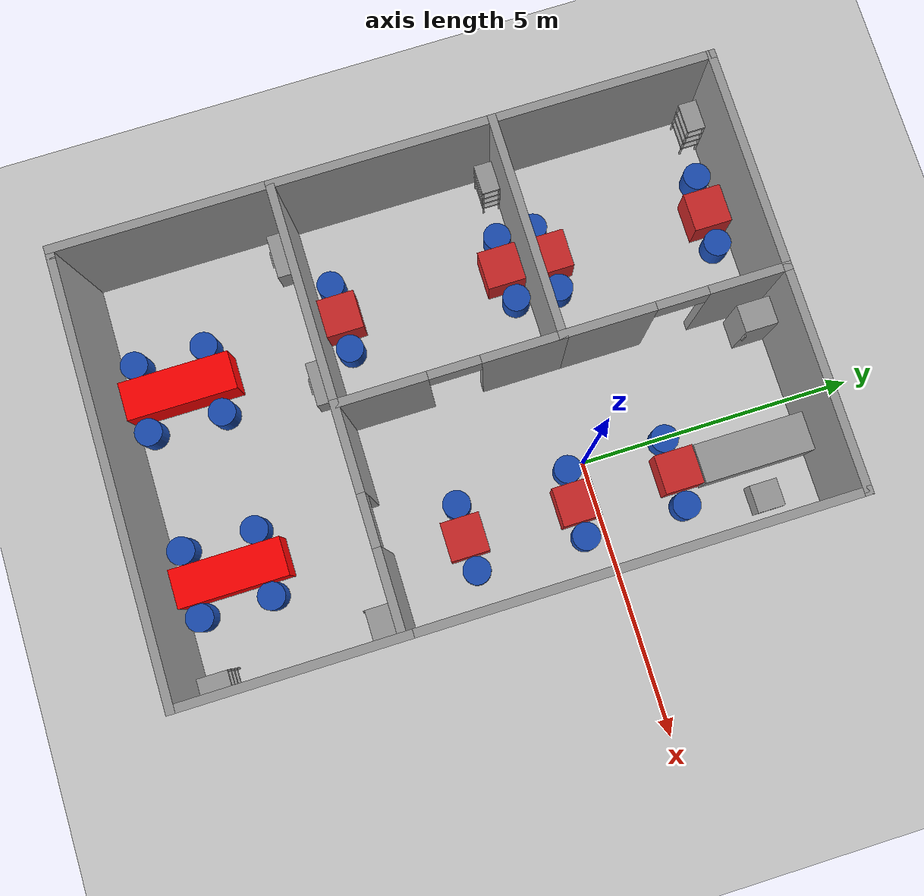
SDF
<sdf version="1.7">
 <world name="default">
  <light name="sun" type="directional">
   <pose>0 0 10 0 -0 0</pose>
   <diffuse>0.8 0.8 0.8 1</diffuse>
   <specular>0.2 0.2 0.2 1</specular>
   <attenuation>
    <range>1000</range>
    <constant>0.9</constant>
    <linear>0.01</linear>
    <quadratic>0.001</quadratic>
   </attenuation>
   <direction>-0.5 0.1 -0.9</direction>
   <spot><inner_angle>0</inner_angle><outer_angle>0</outer_angle><falloff>0</falloff></spot>
  </light>
  <model name="ground_plane">
   <static>1</static>
   <link name="link">
    <collision name="collision">
     <geometry><plane><normal>0 0 1</normal><size>100 100</size></plane></geometry>
     <surface>
      <contact><collide_bitmask>65535</collide_bitmask></contact>
      <friction><ode><mu>100</mu><mu2>50</mu2></ode></friction>
     </surface>
    </collision>
    <visual name="visual">
     <cast_shadows>0</cast_shadows>
     <geometry><plane><normal>0 0 1</normal><size>100 100</size></plane></geometry>
     <material>
      <script><uri>file://media/materials/scripts/gazebo.material</uri><name>Gazebo/Grey</name></script>
     </material>
    </visual>
   </link>
  </model>
  <gravity>0 0 -9.8</gravity>
  <magnetic_field>6e-06 2.3e-05 -4.2e-05</magnetic_field>
  <atmosphere type="adiabatic"/>
  <physics type="ode">
   <max_step_size>0.001</max_step_size>
   <real_time_factor>1</real_time_factor>
   <real_time_update_rate>1000</real_time_update_rate>
  </physics>
  <scene><ambient>0.4 0.4 0.4 1</ambient><background>0.7 0.7 0.7 1</background><shadows>1</shadows></scene>
  <spherical_coordinates>
   <surface_model>EARTH_WGS84</surface_model>
   <latitude_deg>0</latitude_deg>
   <longitude_deg>0</longitude_deg>
   <elevation>0</elevation>
   <heading_deg>0</heading_deg>
  </spherical_coordinates>
  <model name="Room">
   <pose>0.816446 -1.80103 0 0 -0 0</pose>
   <link name="Wall_41">
    <collision name="Wall_41_Collision">
     <geometry><box><size>4 0.15 2.5</size></box></geometry>
     <pose>0 0 1.25 0 -0 0</pose>
    </collision>
    <visual name="Wall_41_Visual">
     <pose>0 0 1.25 0 -0 0</pose>
     <geometry><box><size>4 0.15 2.5</size></box></geometry>
     <material>
      <script><uri>file://media/materials/scripts/gazebo.material</uri><name>Gazebo/Grey</name></script>
      <ambient>1 1 1 1</ambient>
     </material>
     <meta><layer>0</layer></meta>
    </visual>
    <pose>-4.5935 1.875 0 0 -0 0</pose>
   </link>
   <link name="Wall_42">
    <pose>-2.6685 -0.05 0 0 -0 -1.5708</pose>
    <visual name="Wall_42_Visual_0">
     <pose>-1.26796 0 1.25 0 -0 0</pose>
     <geometry><box><size>1.46408 0.15 2.5</size></box></geometry>
     <material>
      <script><uri>file://media/materials/scripts/gazebo.material</uri><name>Gazebo/Grey</name></script>
      <ambient>1 1 1 1</ambient>
     </material>
     <meta><layer>0</layer></meta>
    </visual>
    <collision name="Wall_42_Collision_0">
     <geometry><box><size>1.46408 0.15 2.5</size></box></geometry>
     <pose>-1.26796 0 1.25 0 -0 0</pose>
    </collision>
    <visual name="Wall_42_Visual_1">
     <pose>1.18204 0 1.25 0 -0 0</pose>
     <geometry><box><size>1.63592 0.15 2.5</size></box></geometry>
     <material>
      <script><uri>file://media/materials/scripts/gazebo.material</uri><name>Gazebo/Grey</name></script>
      <ambient>1 1 1 1</ambient>
     </material>
     <meta><layer>0</layer></meta>
    </visual>
    <collision name="Wall_42_Collision_1">
     <geometry><box><size>1.63592 0.15 2.5</size></box></geometry>
     <pose>1.18204 0 1.25 0 -0 0</pose>
    </collision>
    <visual name="Wall_42_Visual_2">
     <pose>-0.085917 0 2.25 0 -0 0</pose>
     <geometry><box><size>0.9 0.15 0.5</size></box></geometry>
     <material>
      <script><uri>file://media/materials/scripts/gazebo.material</uri><name>Gazebo/Grey</name></script>
      <ambient>1 1 1 1</ambient>
     </material>
     <meta><layer>0</layer></meta>
    </visual>
    <collision name="Wall_42_Collision_2">
     <geometry><box><size>0.9 0.15 0.5</size></box></geometry>
     <pose>-0.085917 0 2.25 0 -0 0</pose>
    </collision>
   </link>
   <link name="Wall_43">
    <collision name="Wall_43_Collision">
     <geometry><box><size>4 0.15 2.5</size></box></geometry>
     <pose>0 0 1.25 0 -0 0</pose>
    </collision>
    <visual name="Wall_43_Visual">
     <pose>0 0 1.25 0 -0 0</pose>
     <geometry><box><size>4 0.15 2.5</size></box></geometry>
     <material>
      <script><uri>file://media/materials/scripts/gazebo.material</uri><name>Gazebo/Grey</name></script>
      <ambient>1 1 1 1</ambient>
     </material>
     <meta><layer>0</layer></meta>
    </visual>
    <pose>-4.5935 -1.975 0 0 -0 3.14159</pose>
   </link>
   <link name="Wall_44">
    <collision name="Wall_44_Collision">
     <geometry><box><size>4 0.15 2.5</size></box></geometry>
     <pose>0 0 1.25 0 -0 0</pose>
    </collision>
    <visual name="Wall_44_Visual">
     <pose>0 0 1.25 0 -0 0</pose>
     <geometry><box><size>4 0.15 2.5</size></box></geometry>
     <material>
      <script><uri>file://media/materials/scripts/gazebo.material</uri><name>Gazebo/Grey</name></script>
      <ambient>1 1 1 1</ambient>
     </material>
     <meta><layer>0</layer></meta>
    </visual>
    <pose>-6.5185 -0.05 0 0 -0 1.5708</pose>
   </link>
   <link name="Wall_49">
    <pose>-0.743497 -1.975 0 0 -0 3.14159</pose>
    <visual name="Wall_49_Visual_0">
     <pose>-1.23831 0 1.25 0 -0 0</pose>
     <geometry><box><size>1.52338 0.15 2.5</size></box></geometry>
     <material>
      <script><uri>file://media/materials/scripts/gazebo.material</uri><name>Gazebo/Grey</name></script>
      <ambient>1 1 1 1</ambient>
     </material>
     <meta><layer>0</layer></meta>
    </visual>
    <collision name="Wall_49_Collision_0">
     <geometry><box><size>1.52338 0.15 2.5</size></box></geometry>
     <pose>-1.23831 0 1.25 0 -0 0</pose>
    </collision>
    <visual name="Wall_49_Visual_1">
     <pose>1.21169 0 1.25 0 -0 0</pose>
     <geometry><box><size>1.57662 0.15 2.5</size></box></geometry>
     <material>
      <script><uri>file://media/materials/scripts/gazebo.material</uri><name>Gazebo/Grey</name></script>
      <ambient>1 1 1 1</ambient>
     </material>
     <meta><layer>0</layer></meta>
    </visual>
    <collision name="Wall_49_Collision_1">
     <geometry><box><size>1.57662 0.15 2.5</size></box></geometry>
     <pose>1.21169 0 1.25 0 -0 0</pose>
    </collision>
    <visual name="Wall_49_Visual_2">
     <pose>-0.026623 0 2.25 0 -0 0</pose>
     <geometry><box><size>0.9 0.15 0.5</size></box></geometry>
     <material>
      <script><uri>file://media/materials/scripts/gazebo.material</uri><name>Gazebo/Grey</name></script>
      <ambient>1 1 1 1</ambient>
     </material>
     <meta><layer>0</layer></meta>
    </visual>
    <collision name="Wall_49_Collision_2">
     <geometry><box><size>0.9 0.15 0.5</size></box></geometry>
     <pose>-0.026623 0 2.25 0 -0 0</pose>
    </collision>
   </link>
   <link name="Wall_51">
    <collision name="Wall_51_Collision">
     <geometry><box><size>4 0.15 2.5</size></box></geometry>
     <pose>0 0 1.25 0 -0 0</pose>
    </collision>
    <visual name="Wall_51_Visual">
     <pose>0 0 1.25 0 -0 0</pose>
     <geometry><box><size>4 0.15 2.5</size></box></geometry>
     <material>
      <script><uri>file://media/materials/scripts/gazebo.material</uri><name>Gazebo/Grey</name></script>
      <ambient>1 1 1 1</ambient>
     </material>
     <meta><layer>0</layer></meta>
    </visual>
    <pose>-6.5185 3.8 0 0 -0 1.5708</pose>
   </link>
   <link name="Wall_52">
    <collision name="Wall_52_Collision">
     <geometry><box><size>4 0.15 2.5</size></box></geometry>
     <pose>0 0 1.25 0 -0 0</pose>
    </collision>
    <visual name="Wall_52_Visual">
     <pose>0 0 1.25 0 -0 0</pose>
     <geometry><box><size>4 0.15 2.5</size></box></geometry>
     <material>
      <script><uri>file://media/materials/scripts/gazebo.material</uri><name>Gazebo/Grey</name></script>
      <ambient>1 1 1 1</ambient>
     </material>
     <meta><layer>0</layer></meta>
    </visual>
    <pose>-4.5935 5.725 0 0 -0 0</pose>
   </link>
   <link name="Wall_53">
    <pose>-2.6685 3.8 0 0 -0 -1.5708</pose>
    <visual name="Wall_53_Visual_0">
     <pose>-1.28605 0 1.25 0 -0 0</pose>
     <geometry><box><size>1.42791 0.15 2.5</size></box></geometry>
     <material>
      <script><uri>file://media/materials/scripts/gazebo.material</uri><name>Gazebo/Grey</name></script>
      <ambient>1 1 1 1</ambient>
     </material>
     <meta><layer>0</layer></meta>
    </visual>
    <collision name="Wall_53_Collision_0">
     <geometry><box><size>1.42791 0.15 2.5</size></box></geometry>
     <pose>-1.28605 0 1.25 0 -0 0</pose>
    </collision>
    <visual name="Wall_53_Visual_1">
     <pose>1.16395 0 1.25 0 -0 0</pose>
     <geometry><box><size>1.67209 0.15 2.5</size></box></geometry>
     <material>
      <script><uri>file://media/materials/scripts/gazebo.material</uri><name>Gazebo/Grey</name></script>
      <ambient>1 1 1 1</ambient>
     </material>
     <meta><layer>0</layer></meta>
    </visual>
    <collision name="Wall_53_Collision_1">
     <geometry><box><size>1.67209 0.15 2.5</size></box></geometry>
     <pose>1.16395 0 1.25 0 -0 0</pose>
    </collision>
    <visual name="Wall_53_Visual_2">
     <pose>-0.122091 0 2.25 0 -0 0</pose>
     <geometry><box><size>0.9 0.15 0.5</size></box></geometry>
     <material>
      <script><uri>file://media/materials/scripts/gazebo.material</uri><name>Gazebo/Grey</name></script>
      <ambient>1 1 1 1</ambient>
     </material>
     <meta><layer>0</layer></meta>
    </visual>
    <collision name="Wall_53_Collision_2">
     <geometry><box><size>0.9 0.15 0.5</size></box></geometry>
     <pose>-0.122091 0 2.25 0 -0 0</pose>
    </collision>
   </link>
   <link name="Wall_61">
    <collision name="Wall_61_Collision">
     <geometry><box><size>0.15 0.15 2.5</size></box></geometry>
     <pose>0 0 1.25 0 -0 0</pose>
    </collision>
    <visual name="Wall_61_Visual">
     <pose>0 0 1.25 0 -0 0</pose>
     <geometry><box><size>0.15 0.15 2.5</size></box></geometry>
     <material>
      <script><uri>file://media/materials/scripts/gazebo.material</uri><name>Gazebo/Grey</name></script>
      <ambient>1 1 1 1</ambient>
     </material>
     <meta><layer>0</layer></meta>
    </visual>
    <pose>1.1815 5.725 0 0 -0 0</pose>
   </link>
   <link name="Wall_66">
    <collision name="Wall_66_Collision">
     <geometry><box><size>0.15 0.15 2.5</size></box></geometry>
     <pose>0 0 1.25 0 -0 0</pose>
    </collision>
    <visual name="Wall_66_Visual">
     <pose>0 0 1.25 0 -0 0</pose>
     <geometry><box><size>0.15 0.15 2.5</size></box></geometry>
     <material>
      <script><uri>file://media/materials/scripts/gazebo.material</uri><name>Gazebo/Grey</name></script>
      <ambient>1 1 1 1</ambient>
     </material>
     <meta><layer>0</layer></meta>
    </visual>
    <pose>1.1815 5.725 0 0 -0 0</pose>
   </link>
   <link name="Wall_79">
    <collision name="Wall_79_Collision">
     <geometry><box><size>4 0.15 2.5</size></box></geometry>
     <pose>0 0 1.25 0 -0 0</pose>
    </collision>
    <visual name="Wall_79_Visual">
     <pose>0 0 1.25 0 -0 0</pose>
     <geometry><box><size>4 0.15 2.5</size></box></geometry>
     <material>
      <script><uri>file://media/materials/scripts/gazebo.material</uri><name>Gazebo/Grey</name></script>
      <ambient>1 1 1 1</ambient>
     </material>
     <meta><layer>0</layer></meta>
    </visual>
    <pose>-0.743497 5.725 0 0 -0 0</pose>
   </link>
   <link name="Wall_80">
    <collision name="Wall_80_Collision">
     <geometry><box><size>7.75 0.15 2.5</size></box></geometry>
     <pose>0 0 1.25 0 -0 0</pose>
    </collision>
    <visual name="Wall_80_Visual">
     <pose>0 0 1.25 0 -0 0</pose>
     <geometry><box><size>7.75 0.15 2.5</size></box></geometry>
     <material>
      <script><uri>file://media/materials/scripts/gazebo.material</uri><name>Gazebo/Grey</name></script>
      <ambient>1 1 1 1</ambient>
     </material>
     <meta><layer>0</layer></meta>
    </visual>
    <pose>1.1815 1.925 0 0 -0 -1.5708</pose>
   </link>
   <link name="Wall_82">
    <collision name="Wall_82_Collision">
     <geometry><box><size>4 0.15 2.5</size></box></geometry>
     <pose>0 0 1.25 0 -0 0</pose>
    </collision>
    <visual name="Wall_82_Visual">
     <pose>0 0 1.25 0 -0 0</pose>
     <geometry><box><size>4 0.15 2.5</size></box></geometry>
     <material>
      <script><uri>file://media/materials/scripts/gazebo.material</uri><name>Gazebo/Grey</name></script>
      <ambient>1 1 1 1</ambient>
     </material>
     <meta><layer>0</layer></meta>
    </visual>
    <pose>1.1815 -3.8 0 0 -0 -1.5708</pose>
   </link>
   <link name="Wall_89">
    <collision name="Wall_89_Collision">
     <geometry><box><size>3.9 0.15 2.5</size></box></geometry>
     <pose>0 0 1.25 0 -0 0</pose>
    </collision>
    <visual name="Wall_89_Visual">
     <pose>0 0 1.25 0 -0 0</pose>
     <geometry><box><size>3.9 0.15 2.5</size></box></geometry>
     <material>
      <script><uri>file://media/materials/scripts/gazebo.material</uri><name>Gazebo/Grey</name></script>
      <ambient>1 1 1 1</ambient>
     </material>
     <meta><layer>0</layer></meta>
    </visual>
    <pose>-6.5185 -3.85 0 0 -0 -1.5708</pose>
   </link>
   <link name="Wall_91">
    <collision name="Wall_91_Collision">
     <geometry><box><size>7.75 0.15 2.5</size></box></geometry>
     <pose>0 0 1.25 0 -0 0</pose>
    </collision>
    <visual name="Wall_91_Visual">
     <pose>0 0 1.25 0 -0 0</pose>
     <geometry><box><size>7.75 0.15 2.5</size></box></geometry>
     <material>
      <script><uri>file://media/materials/scripts/gazebo.material</uri><name>Gazebo/Grey</name></script>
      <ambient>1 1 1 1</ambient>
     </material>
     <meta><layer>0</layer></meta>
    </visual>
    <pose>-2.6185 -5.725 0 0 -0 3.14159</pose>
   </link>
   <link name="Wall_92">
    <collision name="Wall_92_Collision">
     <geometry><box><size>0.15 0.15 2.5</size></box></geometry>
     <pose>0 0 1.25 0 -0 0</pose>
    </collision>
    <visual name="Wall_92_Visual">
     <pose>0 0 1.25 0 -0 0</pose>
     <geometry><box><size>0.15 0.15 2.5</size></box></geometry>
     <material>
      <script><uri>file://media/materials/scripts/gazebo.material</uri><name>Gazebo/Grey</name></script>
      <ambient>1 1 1 1</ambient>
     </material>
     <meta><layer>0</layer></meta>
    </visual>
    <pose>-6.4185 -5.725 0 0 -0 0</pose>
   </link>
   <static>1</static>
  </model>
  <model name="Card_table">
   <link name="link">
    <inertial>
     <mass>10</mass>
     <inertia><ixx>1.66667</ixx><ixy>0</ixy><ixz>0</ixz><iyy>1.66667</iyy><iyz>0</iyz><izz>1.66667</izz></inertia>
    </inertial>
    <visual name="visual">
     <geometry><box><size>0.7 0.7 0.7</size></box></geometry>
     <material>
      <script><name>Gazebo/Red</name><uri>file://media/materials/scripts/gazebo.material</uri></script>
      <shader type="vertex"><normal_map>__default__</normal_map></shader>
      <ambient>1 0 0 1</ambient>
      <diffuse>0.9 0.7 0.7 1</diffuse>
      <specular>0.01 0.01 0.01 1</specular>
      <emissive>0 0 0 1</emissive>
     </material>
    </visual>
    <collision name="collision">
     <geometry><box><size>0.7 0.7 0.7</size></box></geometry>
     <surface>
      <friction>
       <ode><mu>1</mu><mu2>1</mu2><fdir1>0 0 0</fdir1><slip1>0</slip1><slip2>0</slip2></ode>
       <torsional>
        <coefficient>1</coefficient>
        <patch_radius>0</patch_radius>
        <surface_radius>0</surface_radius>
        <use_patch_radius>1</use_patch_radius>
        <ode><slip>0</slip></ode>
       </torsional>
      </friction>
      <bounce><restitution_coefficient>0</restitution_coefficient><threshold>1e+06</threshold></bounce>
      <contact>
       <collide_without_contact>0</collide_without_contact>
       <collide_without_contact_bitmask>1</collide_without_contact_bitmask>
       <collide_bitmask>1</collide_bitmask>
       <ode>
        <soft_cfm>0</soft_cfm>
        <soft_erp>0.2</soft_erp>
        <kp>1e+13</kp>
        <kd>1</kd>
        <max_vel>0.01</max_vel>
        <min_depth>0</min_depth>
       </ode>
       <bullet>
        <split_impulse>1</split_impulse>
        <split_impulse_penetration_threshold>-0.01</split_impulse_penetration_threshold>
        <soft_cfm>0</soft_cfm>
        <soft_erp>0.2</soft_erp>
        <kp>1e+13</kp>
        <kd>1</kd>
       </bullet>
      </contact>
     </surface>
    </collision>
   </link>
   <static>1</static>
   <pose>-3.75289 -3.37198 0.35 0 -0 0</pose>
  </model>
  <model name="chair2">
   <link name="link">
    <inertial>
     <mass>1</mass>
     <inertia><ixx>0.145833</ixx><ixy>0</ixy><ixz>0</ixz><iyy>0.145833</iyy><iyz>0</iyz><izz>0.125</izz></inertia>
    </inertial>
    <visual name="visual">
     <geometry><cylinder><radius>0.25</radius><length>0.5</length></cylinder></geometry>
     <material>
      <script><name>Gazebo/Grey</name><uri>file://media/materials/scripts/gazebo.material</uri></script>
      <shader type="pixel"><normal_map>__default__</normal_map></shader>
      <ambient>0.1 0.3 0.7 1</ambient>
      <diffuse>0.7 0.7 0.7 1</diffuse>
      <specular>0.01 0.01 0.01 1</specular>
      <emissive>0 0 0 1</emissive>
     </material>
    </visual>
    <collision name="collision">
     <geometry><cylinder><radius>0.25</radius><length>0.5</length></cylinder></geometry>
     <surface>
      <friction>
       <ode><mu>1</mu><mu2>1</mu2><fdir1>0 0 0</fdir1><slip1>0</slip1><slip2>0</slip2></ode>
       <torsional>
        <coefficient>1</coefficient>
        <patch_radius>0</patch_radius>
        <surface_radius>0</surface_radius>
        <use_patch_radius>1</use_patch_radius>
        <ode><slip>0</slip></ode>
       </torsional>
      </friction>
      <bounce><restitution_coefficient>0</restitution_coefficient><threshold>1e+06</threshold></bounce>
      <contact>
       <collide_without_contact>0</collide_without_contact>
       <collide_without_contact_bitmask>1</collide_without_contact_bitmask>
       <collide_bitmask>1</collide_bitmask>
       <ode>
        <soft_cfm>0</soft_cfm>
        <soft_erp>0.2</soft_erp>
        <kp>1e+13</kp>
        <kd>1</kd>
        <max_vel>0.01</max_vel>
        <min_depth>0</min_depth>
       </ode>
       <bullet>
        <split_impulse>1</split_impulse>
        <split_impulse_penetration_threshold>-0.01</split_impulse_penetration_threshold>
        <soft_cfm>0</soft_cfm>
        <soft_erp>0.2</soft_erp>
        <kp>1e+13</kp>
        <kd>1</kd>
       </bullet>
      </contact>
     </surface>
    </collision>
   </link>
   <static>1</static>
   <pose>-4.37303 -3.38534 0.25 0 -0 0</pose>
  </model>
  <model name="chair2_clone">
   <link name="link">
    <inertial>
     <mass>1</mass>
     <inertia><ixx>0.145833</ixx><ixy>0</ixy><ixz>0</ixz><iyy>0.145833</iyy><iyz>0</iyz><izz>0.125</izz></inertia>
    </inertial>
    <visual name="visual">
     <geometry><cylinder><radius>0.25</radius><length>0.5</length></cylinder></geometry>
     <material>
      <script><name>Gazebo/Grey</name><uri>file://media/materials/scripts/gazebo.material</uri></script>
      <shader type="pixel"><normal_map>__default__</normal_map></shader>
      <ambient>0.1 0.3 0.7 1</ambient>
      <diffuse>0.7 0.7 0.7 1</diffuse>
      <specular>0.01 0.01 0.01 1</specular>
      <emissive>0 0 0 1</emissive>
     </material>
    </visual>
    <collision name="collision">
     <geometry><cylinder><radius>0.25</radius><length>0.5</length></cylinder></geometry>
     <surface>
      <friction>
       <ode><mu>1</mu><mu2>1</mu2><fdir1>0 0 0</fdir1><slip1>0</slip1><slip2>0</slip2></ode>
       <torsional>
        <coefficient>1</coefficient>
        <patch_radius>0</patch_radius>
        <surface_radius>0</surface_radius>
        <use_patch_radius>1</use_patch_radius>
        <ode><slip>0</slip></ode>
       </torsional>
      </friction>
      <bounce><restitution_coefficient>0</restitution_coefficient><threshold>1e+06</threshold></bounce>
      <contact>
       <collide_without_contact>0</collide_without_contact>
       <collide_without_contact_bitmask>1</collide_without_contact_bitmask>
       <collide_bitmask>1</collide_bitmask>
       <ode>
        <soft_cfm>0</soft_cfm>
        <soft_erp>0.2</soft_erp>
        <kp>1e+13</kp>
        <kd>1</kd>
        <max_vel>0.01</max_vel>
        <min_depth>0</min_depth>
       </ode>
       <bullet>
        <split_impulse>1</split_impulse>
        <split_impulse_penetration_threshold>-0.01</split_impulse_penetration_threshold>
        <soft_cfm>0</soft_cfm>
        <soft_erp>0.2</soft_erp>
        <kp>1e+13</kp>
        <kd>1</kd>
       </bullet>
      </contact>
     </surface>
    </collision>
   </link>
   <static>1</static>
   <pose>-4.34714 -0.258544 0.25 0 -0 0</pose>
  </model>
  <model name="chair2_clone_0">
   <link name="link">
    <inertial>
     <mass>1</mass>
     <inertia><ixx>0.145833</ixx><ixy>0</ixy><ixz>0</ixz><iyy>0.145833</iyy><iyz>0</iyz><izz>0.125</izz></inertia>
    </inertial>
    <visual name="visual">
     <geometry><cylinder><radius>0.25</radius><length>0.5</length></cylinder></geometry>
     <material>
      <script><name>Gazebo/Grey</name><uri>file://media/materials/scripts/gazebo.material</uri></script>
      <shader type="pixel"><normal_map>__default__</normal_map></shader>
      <ambient>0.1 0.3 0.7 1</ambient>
      <diffuse>0.7 0.7 0.7 1</diffuse>
      <specular>0.01 0.01 0.01 1</specular>
      <emissive>0 0 0 1</emissive>
     </material>
    </visual>
    <collision name="collision">
     <geometry><cylinder><radius>0.25</radius><length>0.5</length></cylinder></geometry>
     <surface>
      <friction>
       <ode><mu>1</mu><mu2>1</mu2><fdir1>0 0 0</fdir1><slip1>0</slip1><slip2>0</slip2></ode>
       <torsional>
        <coefficient>1</coefficient>
        <patch_radius>0</patch_radius>
        <surface_radius>0</surface_radius>
        <use_patch_radius>1</use_patch_radius>
        <ode><slip>0</slip></ode>
       </torsional>
      </friction>
      <bounce><restitution_coefficient>0</restitution_coefficient><threshold>1e+06</threshold></bounce>
      <contact>
       <collide_without_contact>0</collide_without_contact>
       <collide_without_contact_bitmask>1</collide_without_contact_bitmask>
       <collide_bitmask>1</collide_bitmask>
       <ode>
        <soft_cfm>0</soft_cfm>
        <soft_erp>0.2</soft_erp>
        <kp>1e+13</kp>
        <kd>1</kd>
        <max_vel>0.01</max_vel>
        <min_depth>0</min_depth>
       </ode>
       <bullet>
        <split_impulse>1</split_impulse>
        <split_impulse_penetration_threshold>-0.01</split_impulse_penetration_threshold>
        <soft_cfm>0</soft_cfm>
        <soft_erp>0.2</soft_erp>
        <kp>1e+13</kp>
        <kd>1</kd>
       </bullet>
      </contact>
     </surface>
    </collision>
   </link>
   <static>1</static>
   <pose>-3.14555 -3.37656 0.25 0 -0 0</pose>
  </model>
  <model name="chair2_clone_1">
   <link name="link">
    <inertial>
     <mass>1</mass>
     <inertia><ixx>0.145833</ixx><ixy>0</ixy><ixz>0</ixz><iyy>0.145833</iyy><iyz>0</iyz><izz>0.125</izz></inertia>
    </inertial>
    <visual name="visual">
     <geometry><cylinder><radius>0.25</radius><length>0.5</length></cylinder></geometry>
     <material>
      <script><name>Gazebo/Grey</name><uri>file://media/materials/scripts/gazebo.material</uri></script>
      <shader type="pixel"><normal_map>__default__</normal_map></shader>
      <ambient>0.1 0.3 0.7 1</ambient>
      <diffuse>0.7 0.7 0.7 1</diffuse>
      <specular>0.01 0.01 0.01 1</specular>
      <emissive>0 0 0 1</emissive>
     </material>
    </visual>
    <collision name="collision">
     <geometry><cylinder><radius>0.25</radius><length>0.5</length></cylinder></geometry>
     <surface>
      <friction>
       <ode><mu>1</mu><mu2>1</mu2><fdir1>0 0 0</fdir1><slip1>0</slip1><slip2>0</slip2></ode>
       <torsional>
        <coefficient>1</coefficient>
        <patch_radius>0</patch_radius>
        <surface_radius>0</surface_radius>
        <use_patch_radius>1</use_patch_radius>
        <ode><slip>0</slip></ode>
       </torsional>
      </friction>
      <bounce><restitution_coefficient>0</restitution_coefficient><threshold>1e+06</threshold></bounce>
      <contact>
       <collide_without_contact>0</collide_without_contact>
       <collide_without_contact_bitmask>1</collide_without_contact_bitmask>
       <collide_bitmask>1</collide_bitmask>
       <ode>
        <soft_cfm>0</soft_cfm>
        <soft_erp>0.2</soft_erp>
        <kp>1e+13</kp>
        <kd>1</kd>
        <max_vel>0.01</max_vel>
        <min_depth>0</min_depth>
       </ode>
       <bullet>
        <split_impulse>1</split_impulse>
        <split_impulse_penetration_threshold>-0.01</split_impulse_penetration_threshold>
        <soft_cfm>0</soft_cfm>
        <soft_erp>0.2</soft_erp>
        <kp>1e+13</kp>
        <kd>1</kd>
       </bullet>
      </contact>
     </surface>
    </collision>
   </link>
   <static>1</static>
   <pose>-3.15619 -0.26133 0.25 0 -0 0</pose>
  </model>
  <model name="Card_table_clone">
   <link name="link">
    <inertial>
     <mass>10</mass>
     <inertia><ixx>1.66667</ixx><ixy>0</ixy><ixz>0</ixz><iyy>1.66667</iyy><iyz>0</iyz><izz>1.66667</izz></inertia>
    </inertial>
    <visual name="visual">
     <geometry><box><size>0.7 0.7 0.7</size></box></geometry>
     <material>
      <script><name>Gazebo/Red</name><uri>file://media/materials/scripts/gazebo.material</uri></script>
      <shader type="vertex"><normal_map>__default__</normal_map></shader>
      <ambient>1 0 0 1</ambient>
      <diffuse>0.9 0.7 0.7 1</diffuse>
      <specular>0.01 0.01 0.01 1</specular>
      <emissive>0 0 0 1</emissive>
     </material>
    </visual>
    <collision name="collision">
     <geometry><box><size>0.7 0.7 0.7</size></box></geometry>
     <surface>
      <friction>
       <ode><mu>1</mu><mu2>1</mu2><fdir1>0 0 0</fdir1><slip1>0</slip1><slip2>0</slip2></ode>
       <torsional>
        <coefficient>1</coefficient>
        <patch_radius>0</patch_radius>
        <surface_radius>0</surface_radius>
        <use_patch_radius>1</use_patch_radius>
        <ode><slip>0</slip></ode>
       </torsional>
      </friction>
      <bounce><restitution_coefficient>0</restitution_coefficient><threshold>1e+06</threshold></bounce>
      <contact>
       <collide_without_contact>0</collide_without_contact>
       <collide_without_contact_bitmask>1</collide_without_contact_bitmask>
       <collide_bitmask>1</collide_bitmask>
       <ode>
        <soft_cfm>0</soft_cfm>
        <soft_erp>0.2</soft_erp>
        <kp>1e+13</kp>
        <kd>1</kd>
        <max_vel>0.01</max_vel>
        <min_depth>0</min_depth>
       </ode>
       <bullet>
        <split_impulse>1</split_impulse>
        <split_impulse_penetration_threshold>-0.01</split_impulse_penetration_threshold>
        <soft_cfm>0</soft_cfm>
        <soft_erp>0.2</soft_erp>
        <kp>1e+13</kp>
        <kd>1</kd>
       </bullet>
      </contact>
     </surface>
    </collision>
   </link>
   <static>1</static>
   <pose>-3.74721 -0.360539 0.35 0 -0 0</pose>
  </model>
  <model name="Card_table_clone_clone">
   <link name="link">
    <inertial>
     <mass>10</mass>
     <inertia><ixx>1.66667</ixx><ixy>0</ixy><ixz>0</ixz><iyy>1.66667</iyy><iyz>0</iyz><izz>1.66667</izz></inertia>
    </inertial>
    <visual name="visual">
     <geometry><box><size>0.7 0.7 0.7</size></box></geometry>
     <material>
      <script><name>Gazebo/Red</name><uri>file://media/materials/scripts/gazebo.material</uri></script>
      <shader type="vertex"><normal_map>__default__</normal_map></shader>
      <ambient>1 0 0 1</ambient>
      <diffuse>0.9 0.7 0.7 1</diffuse>
      <specular>0.01 0.01 0.01 1</specular>
      <emissive>0 0 0 1</emissive>
     </material>
    </visual>
    <collision name="collision">
     <geometry><box><size>0.7 0.7 0.7</size></box></geometry>
     <surface>
      <friction>
       <ode><mu>1</mu><mu2>1</mu2><fdir1>0 0 0</fdir1><slip1>0</slip1><slip2>0</slip2></ode>
       <torsional>
        <coefficient>1</coefficient>
        <patch_radius>0</patch_radius>
        <surface_radius>0</surface_radius>
        <use_patch_radius>1</use_patch_radius>
        <ode><slip>0</slip></ode>
       </torsional>
      </friction>
      <bounce><restitution_coefficient>0</restitution_coefficient><threshold>1e+06</threshold></bounce>
      <contact>
       <collide_without_contact>0</collide_without_contact>
       <collide_without_contact_bitmask>1</collide_without_contact_bitmask>
       <collide_bitmask>1</collide_bitmask>
       <ode>
        <soft_cfm>0</soft_cfm>
        <soft_erp>0.2</soft_erp>
        <kp>1e+13</kp>
        <kd>1</kd>
        <max_vel>0.01</max_vel>
        <min_depth>0</min_depth>
       </ode>
       <bullet>
        <split_impulse>1</split_impulse>
        <split_impulse_penetration_threshold>-0.01</split_impulse_penetration_threshold>
        <soft_cfm>0</soft_cfm>
        <soft_erp>0.2</soft_erp>
        <kp>1e+13</kp>
        <kd>1</kd>
       </bullet>
      </contact>
     </surface>
    </collision>
   </link>
   <static>1</static>
   <pose>-3.72304 0.537084 0.35 0 -0 0</pose>
  </model>
  <model name="chair2_clone_clone">
   <link name="link">
    <inertial>
     <mass>1</mass>
     <inertia><ixx>0.145833</ixx><ixy>0</ixy><ixz>0</ixz><iyy>0.145833</iyy><iyz>0</iyz><izz>0.125</izz></inertia>
    </inertial>
    <visual name="visual">
     <geometry><cylinder><radius>0.25</radius><length>0.5</length></cylinder></geometry>
     <material>
      <script><name>Gazebo/Grey</name><uri>file://media/materials/scripts/gazebo.material</uri></script>
      <shader type="pixel"><normal_map>__default__</normal_map></shader>
      <ambient>0.1 0.3 0.7 1</ambient>
      <diffuse>0.7 0.7 0.7 1</diffuse>
      <specular>0.01 0.01 0.01 1</specular>
      <emissive>0 0 0 1</emissive>
     </material>
    </visual>
    <collision name="collision">
     <geometry><cylinder><radius>0.25</radius><length>0.5</length></cylinder></geometry>
     <surface>
      <friction>
       <ode><mu>1</mu><mu2>1</mu2><fdir1>0 0 0</fdir1><slip1>0</slip1><slip2>0</slip2></ode>
       <torsional>
        <coefficient>1</coefficient>
        <patch_radius>0</patch_radius>
        <surface_radius>0</surface_radius>
        <use_patch_radius>1</use_patch_radius>
        <ode><slip>0</slip></ode>
       </torsional>
      </friction>
      <bounce><restitution_coefficient>0</restitution_coefficient><threshold>1e+06</threshold></bounce>
      <contact>
       <collide_without_contact>0</collide_without_contact>
       <collide_without_contact_bitmask>1</collide_without_contact_bitmask>
       <collide_bitmask>1</collide_bitmask>
       <ode>
        <soft_cfm>0</soft_cfm>
        <soft_erp>0.2</soft_erp>
        <kp>1e+13</kp>
        <kd>1</kd>
        <max_vel>0.01</max_vel>
        <min_depth>0</min_depth>
       </ode>
       <bullet>
        <split_impulse>1</split_impulse>
        <split_impulse_penetration_threshold>-0.01</split_impulse_penetration_threshold>
        <soft_cfm>0</soft_cfm>
        <soft_erp>0.2</soft_erp>
        <kp>1e+13</kp>
        <kd>1</kd>
       </bullet>
      </contact>
     </surface>
    </collision>
   </link>
   <static>1</static>
   <pose>-4.3235 0.422897 0.25 0 -0 0</pose>
  </model>
  <model name="chair2_clone_2">
   <link name="link">
    <inertial>
     <mass>1</mass>
     <inertia><ixx>0.145833</ixx><ixy>0</ixy><ixz>0</ixz><iyy>0.145833</iyy><iyz>0</iyz><izz>0.125</izz></inertia>
    </inertial>
    <visual name="visual">
     <geometry><cylinder><radius>0.25</radius><length>0.5</length></cylinder></geometry>
     <material>
      <script><name>Gazebo/Grey</name><uri>file://media/materials/scripts/gazebo.material</uri></script>
      <shader type="pixel"><normal_map>__default__</normal_map></shader>
      <ambient>0.1 0.3 0.7 1</ambient>
      <diffuse>0.7 0.7 0.7 1</diffuse>
      <specular>0.01 0.01 0.01 1</specular>
      <emissive>0 0 0 1</emissive>
     </material>
    </visual>
    <collision name="collision">
     <geometry><cylinder><radius>0.25</radius><length>0.5</length></cylinder></geometry>
     <surface>
      <friction>
       <ode><mu>1</mu><mu2>1</mu2><fdir1>0 0 0</fdir1><slip1>0</slip1><slip2>0</slip2></ode>
       <torsional>
        <coefficient>1</coefficient>
        <patch_radius>0</patch_radius>
        <surface_radius>0</surface_radius>
        <use_patch_radius>1</use_patch_radius>
        <ode><slip>0</slip></ode>
       </torsional>
      </friction>
      <bounce><restitution_coefficient>0</restitution_coefficient><threshold>1e+06</threshold></bounce>
      <contact>
       <collide_without_contact>0</collide_without_contact>
       <collide_without_contact_bitmask>1</collide_without_contact_bitmask>
       <collide_bitmask>1</collide_bitmask>
       <ode>
        <soft_cfm>0</soft_cfm>
        <soft_erp>0.2</soft_erp>
        <kp>1e+13</kp>
        <kd>1</kd>
        <max_vel>0.01</max_vel>
        <min_depth>0</min_depth>
       </ode>
       <bullet>
        <split_impulse>1</split_impulse>
        <split_impulse_penetration_threshold>-0.01</split_impulse_penetration_threshold>
        <soft_cfm>0</soft_cfm>
        <soft_erp>0.2</soft_erp>
        <kp>1e+13</kp>
        <kd>1</kd>
       </bullet>
      </contact>
     </surface>
    </collision>
   </link>
   <static>1</static>
   <pose>-4.35825 3.56614 0.25 0 -0 0</pose>
  </model>
  <model name="chair2_clone_3">
   <link name="link">
    <inertial>
     <mass>1</mass>
     <inertia><ixx>0.145833</ixx><ixy>0</ixy><ixz>0</ixz><iyy>0.145833</iyy><iyz>0</iyz><izz>0.125</izz></inertia>
    </inertial>
    <visual name="visual">
     <geometry><cylinder><radius>0.25</radius><length>0.5</length></cylinder></geometry>
     <material>
      <script><name>Gazebo/Grey</name><uri>file://media/materials/scripts/gazebo.material</uri></script>
      <shader type="pixel"><normal_map>__default__</normal_map></shader>
      <ambient>0.1 0.3 0.7 1</ambient>
      <diffuse>0.7 0.7 0.7 1</diffuse>
      <specular>0.01 0.01 0.01 1</specular>
      <emissive>0 0 0 1</emissive>
     </material>
    </visual>
    <collision name="collision">
     <geometry><cylinder><radius>0.25</radius><length>0.5</length></cylinder></geometry>
     <surface>
      <friction>
       <ode><mu>1</mu><mu2>1</mu2><fdir1>0 0 0</fdir1><slip1>0</slip1><slip2>0</slip2></ode>
       <torsional>
        <coefficient>1</coefficient>
        <patch_radius>0</patch_radius>
        <surface_radius>0</surface_radius>
        <use_patch_radius>1</use_patch_radius>
        <ode><slip>0</slip></ode>
       </torsional>
      </friction>
      <bounce><restitution_coefficient>0</restitution_coefficient><threshold>1e+06</threshold></bounce>
      <contact>
       <collide_without_contact>0</collide_without_contact>
       <collide_without_contact_bitmask>1</collide_without_contact_bitmask>
       <collide_bitmask>1</collide_bitmask>
       <ode>
        <soft_cfm>0</soft_cfm>
        <soft_erp>0.2</soft_erp>
        <kp>1e+13</kp>
        <kd>1</kd>
        <max_vel>0.01</max_vel>
        <min_depth>0</min_depth>
       </ode>
       <bullet>
        <split_impulse>1</split_impulse>
        <split_impulse_penetration_threshold>-0.01</split_impulse_penetration_threshold>
        <soft_cfm>0</soft_cfm>
        <soft_erp>0.2</soft_erp>
        <kp>1e+13</kp>
        <kd>1</kd>
       </bullet>
      </contact>
     </surface>
    </collision>
   </link>
   <static>1</static>
   <pose>-3.05884 3.51855 0.25 0 -0 0</pose>
  </model>
  <model name="Card_table_clone_0">
   <link name="link">
    <inertial>
     <mass>10</mass>
     <inertia><ixx>1.66667</ixx><ixy>0</ixy><ixz>0</ixz><iyy>1.66667</iyy><iyz>0</iyz><izz>1.66667</izz></inertia>
    </inertial>
    <visual name="visual">
     <geometry><box><size>0.7 0.7 0.7</size></box></geometry>
     <material>
      <script><name>Gazebo/Red</name><uri>file://media/materials/scripts/gazebo.material</uri></script>
      <shader type="vertex"><normal_map>__default__</normal_map></shader>
      <ambient>1 0 0 1</ambient>
      <diffuse>0.9 0.7 0.7 1</diffuse>
      <specular>0.01 0.01 0.01 1</specular>
      <emissive>0 0 0 1</emissive>
     </material>
    </visual>
    <collision name="collision">
     <geometry><box><size>0.7 0.7 0.7</size></box></geometry>
     <surface>
      <friction>
       <ode><mu>1</mu><mu2>1</mu2><fdir1>0 0 0</fdir1><slip1>0</slip1><slip2>0</slip2></ode>
       <torsional>
        <coefficient>1</coefficient>
        <patch_radius>0</patch_radius>
        <surface_radius>0</surface_radius>
        <use_patch_radius>1</use_patch_radius>
        <ode><slip>0</slip></ode>
       </torsional>
      </friction>
      <bounce><restitution_coefficient>0</restitution_coefficient><threshold>1e+06</threshold></bounce>
      <contact>
       <collide_without_contact>0</collide_without_contact>
       <collide_without_contact_bitmask>1</collide_without_contact_bitmask>
       <collide_bitmask>1</collide_bitmask>
       <ode>
        <soft_cfm>0</soft_cfm>
        <soft_erp>0.2</soft_erp>
        <kp>1e+13</kp>
        <kd>1</kd>
        <max_vel>0.01</max_vel>
        <min_depth>0</min_depth>
       </ode>
       <bullet>
        <split_impulse>1</split_impulse>
        <split_impulse_penetration_threshold>-0.01</split_impulse_penetration_threshold>
        <soft_cfm>0</soft_cfm>
        <soft_erp>0.2</soft_erp>
        <kp>1e+13</kp>
        <kd>1</kd>
       </bullet>
      </contact>
     </surface>
    </collision>
   </link>
   <static>1</static>
   <pose>-3.67958 3.50831 0.35 0 -0 0</pose>
  </model>
  <model name="table2">
   <link name="link">
    <inertial>
     <mass>1</mass>
     <inertia>
      <ixx>0.166667</ixx>
      <ixy>0</ixy>
      <ixz>0</ixz>
      <iyy>0.166667</iyy>
      <iyz>0</iyz>
      <izz>0.166667</izz>
     </inertia>
    </inertial>
    <visual name="visual">
     <geometry><box><size>2 0.7 0.7</size></box></geometry>
     <material>
      <script><name>Gazebo/Grey</name><uri>file://media/materials/scripts/gazebo.material</uri></script>
      <shader type="pixel"><normal_map>__default__</normal_map></shader>
      <ambient>1 0 0 1</ambient>
      <diffuse>0.7 0.7 0.7 1</diffuse>
      <specular>0.01 0.01 0.01 1</specular>
      <emissive>0 0 0 1</emissive>
     </material>
    </visual>
    <collision name="collision">
     <geometry><box><size>2 0.7 0.7</size></box></geometry>
     <surface>
      <friction>
       <ode><mu>1</mu><mu2>1</mu2><fdir1>0 0 0</fdir1><slip1>0</slip1><slip2>0</slip2></ode>
       <torsional>
        <coefficient>1</coefficient>
        <patch_radius>0</patch_radius>
        <surface_radius>0</surface_radius>
        <use_patch_radius>1</use_patch_radius>
        <ode><slip>0</slip></ode>
       </torsional>
      </friction>
      <bounce><restitution_coefficient>0</restitution_coefficient><threshold>1e+06</threshold></bounce>
      <contact>
       <collide_without_contact>0</collide_without_contact>
       <collide_without_contact_bitmask>1</collide_without_contact_bitmask>
       <collide_bitmask>1</collide_bitmask>
       <ode>
        <soft_cfm>0</soft_cfm>
        <soft_erp>0.2</soft_erp>
        <kp>1e+13</kp>
        <kd>1</kd>
        <max_vel>0.01</max_vel>
        <min_depth>0</min_depth>
       </ode>
       <bullet>
        <split_impulse>1</split_impulse>
        <split_impulse_penetration_threshold>-0.01</split_impulse_penetration_threshold>
        <soft_cfm>0</soft_cfm>
        <soft_erp>0.2</soft_erp>
        <kp>1e+13</kp>
        <kd>1</kd>
       </bullet>
      </contact>
     </surface>
    </collision>
   </link>
   <static>1</static>
   <pose>-3.35345 -6.45251 0.35 0 -0 1.57</pose>
  </model>
  <model name="chair2_clone_4">
   <link name="link">
    <inertial>
     <mass>1</mass>
     <inertia><ixx>0.145833</ixx><ixy>0</ixy><ixz>0</ixz><iyy>0.145833</iyy><iyz>0</iyz><izz>0.125</izz></inertia>
    </inertial>
    <visual name="visual">
     <geometry><cylinder><radius>0.25</radius><length>0.5</length></cylinder></geometry>
     <material>
      <script><name>Gazebo/Grey</name><uri>file://media/materials/scripts/gazebo.material</uri></script>
      <shader type="pixel"><normal_map>__default__</normal_map></shader>
      <ambient>0.1 0.3 0.7 1</ambient>
      <diffuse>0.7 0.7 0.7 1</diffuse>
      <specular>0.01 0.01 0.01 1</specular>
      <emissive>0 0 0 1</emissive>
     </material>
    </visual>
    <collision name="collision">
     <geometry><cylinder><radius>0.25</radius><length>0.5</length></cylinder></geometry>
     <surface>
      <friction>
       <ode><mu>1</mu><mu2>1</mu2><fdir1>0 0 0</fdir1><slip1>0</slip1><slip2>0</slip2></ode>
       <torsional>
        <coefficient>1</coefficient>
        <patch_radius>0</patch_radius>
        <surface_radius>0</surface_radius>
        <use_patch_radius>1</use_patch_radius>
        <ode><slip>0</slip></ode>
       </torsional>
      </friction>
      <bounce><restitution_coefficient>0</restitution_coefficient><threshold>1e+06</threshold></bounce>
      <contact>
       <collide_without_contact>0</collide_without_contact>
       <collide_without_contact_bitmask>1</collide_without_contact_bitmask>
       <collide_bitmask>1</collide_bitmask>
       <ode>
        <soft_cfm>0</soft_cfm>
        <soft_erp>0.2</soft_erp>
        <kp>1e+13</kp>
        <kd>1</kd>
        <max_vel>0.01</max_vel>
        <min_depth>0</min_depth>
       </ode>
       <bullet>
        <split_impulse>1</split_impulse>
        <split_impulse_penetration_threshold>-0.01</split_impulse_penetration_threshold>
        <soft_cfm>0</soft_cfm>
        <soft_erp>0.2</soft_erp>
        <kp>1e+13</kp>
        <kd>1</kd>
       </bullet>
      </contact>
     </surface>
    </collision>
   </link>
   <static>1</static>
   <pose>-3.98866 -7.13646 0.25 0 -0 0</pose>
  </model>
  <model name="chair2_clone_5">
   <link name="link">
    <inertial>
     <mass>1</mass>
     <inertia><ixx>0.145833</ixx><ixy>0</ixy><ixz>0</ixz><iyy>0.145833</iyy><iyz>0</iyz><izz>0.125</izz></inertia>
    </inertial>
    <visual name="visual">
     <geometry><cylinder><radius>0.25</radius><length>0.5</length></cylinder></geometry>
     <material>
      <script><name>Gazebo/Grey</name><uri>file://media/materials/scripts/gazebo.material</uri></script>
      <shader type="pixel"><normal_map>__default__</normal_map></shader>
      <ambient>0.1 0.3 0.7 1</ambient>
      <diffuse>0.7 0.7 0.7 1</diffuse>
      <specular>0.01 0.01 0.01 1</specular>
      <emissive>0 0 0 1</emissive>
     </material>
    </visual>
    <collision name="collision">
     <geometry><cylinder><radius>0.25</radius><length>0.5</length></cylinder></geometry>
     <surface>
      <friction>
       <ode><mu>1</mu><mu2>1</mu2><fdir1>0 0 0</fdir1><slip1>0</slip1><slip2>0</slip2></ode>
       <torsional>
        <coefficient>1</coefficient>
        <patch_radius>0</patch_radius>
        <surface_radius>0</surface_radius>
        <use_patch_radius>1</use_patch_radius>
        <ode><slip>0</slip></ode>
       </torsional>
      </friction>
      <bounce><restitution_coefficient>0</restitution_coefficient><threshold>1e+06</threshold></bounce>
      <contact>
       <collide_without_contact>0</collide_without_contact>
       <collide_without_contact_bitmask>1</collide_without_contact_bitmask>
       <collide_bitmask>1</collide_bitmask>
       <ode>
        <soft_cfm>0</soft_cfm>
        <soft_erp>0.2</soft_erp>
        <kp>1e+13</kp>
        <kd>1</kd>
        <max_vel>0.01</max_vel>
        <min_depth>0</min_depth>
       </ode>
       <bullet>
        <split_impulse>1</split_impulse>
        <split_impulse_penetration_threshold>-0.01</split_impulse_penetration_threshold>
        <soft_cfm>0</soft_cfm>
        <soft_erp>0.2</soft_erp>
        <kp>1e+13</kp>
        <kd>1</kd>
       </bullet>
      </contact>
     </surface>
    </collision>
   </link>
   <static>1</static>
   <pose>-3.96948 -5.85962 0.25 0 -0 0</pose>
  </model>
  <model name="chair2_clone_4_clone">
   <link name="link">
    <inertial>
     <mass>1</mass>
     <inertia><ixx>0.145833</ixx><ixy>0</ixy><ixz>0</ixz><iyy>0.145833</iyy><iyz>0</iyz><izz>0.125</izz></inertia>
    </inertial>
    <visual name="visual">
     <geometry><cylinder><radius>0.25</radius><length>0.5</length></cylinder></geometry>
     <material>
      <script><name>Gazebo/Grey</name><uri>file://media/materials/scripts/gazebo.material</uri></script>
      <shader type="pixel"><normal_map>__default__</normal_map></shader>
      <ambient>0.1 0.3 0.7 1</ambient>
      <diffuse>0.7 0.7 0.7 1</diffuse>
      <specular>0.01 0.01 0.01 1</specular>
      <emissive>0 0 0 1</emissive>
     </material>
    </visual>
    <collision name="collision">
     <geometry><cylinder><radius>0.25</radius><length>0.5</length></cylinder></geometry>
     <surface>
      <friction>
       <ode><mu>1</mu><mu2>1</mu2><fdir1>0 0 0</fdir1><slip1>0</slip1><slip2>0</slip2></ode>
       <torsional>
        <coefficient>1</coefficient>
        <patch_radius>0</patch_radius>
        <surface_radius>0</surface_radius>
        <use_patch_radius>1</use_patch_radius>
        <ode><slip>0</slip></ode>
       </torsional>
      </friction>
      <bounce><restitution_coefficient>0</restitution_coefficient><threshold>1e+06</threshold></bounce>
      <contact>
       <collide_without_contact>0</collide_without_contact>
       <collide_without_contact_bitmask>1</collide_without_contact_bitmask>
       <collide_bitmask>1</collide_bitmask>
       <ode>
        <soft_cfm>0</soft_cfm>
        <soft_erp>0.2</soft_erp>
        <kp>1e+13</kp>
        <kd>1</kd>
        <max_vel>0.01</max_vel>
        <min_depth>0</min_depth>
       </ode>
       <bullet>
        <split_impulse>1</split_impulse>
        <split_impulse_penetration_threshold>-0.01</split_impulse_penetration_threshold>
        <soft_cfm>0</soft_cfm>
        <soft_erp>0.2</soft_erp>
        <kp>1e+13</kp>
        <kd>1</kd>
       </bullet>
      </contact>
     </surface>
    </collision>
   </link>
   <static>1</static>
   <pose>-2.74988 -7.19832 0.25 0 -0 0</pose>
  </model>
  <model name="chair2_clone_4_clone_0">
   <link name="link">
    <inertial>
     <mass>1</mass>
     <inertia><ixx>0.145833</ixx><ixy>0</ixy><ixz>0</ixz><iyy>0.145833</iyy><iyz>0</iyz><izz>0.125</izz></inertia>
    </inertial>
    <visual name="visual">
     <geometry><cylinder><radius>0.25</radius><length>0.5</length></cylinder></geometry>
     <material>
      <script><name>Gazebo/Grey</name><uri>file://media/materials/scripts/gazebo.material</uri></script>
      <shader type="pixel"><normal_map>__default__</normal_map></shader>
      <ambient>0.1 0.3 0.7 1</ambient>
      <diffuse>0.7 0.7 0.7 1</diffuse>
      <specular>0.01 0.01 0.01 1</specular>
      <emissive>0 0 0 1</emissive>
     </material>
    </visual>
    <collision name="collision">
     <geometry><cylinder><radius>0.25</radius><length>0.5</length></cylinder></geometry>
     <surface>
      <friction>
       <ode><mu>1</mu><mu2>1</mu2><fdir1>0 0 0</fdir1><slip1>0</slip1><slip2>0</slip2></ode>
       <torsional>
        <coefficient>1</coefficient>
        <patch_radius>0</patch_radius>
        <surface_radius>0</surface_radius>
        <use_patch_radius>1</use_patch_radius>
        <ode><slip>0</slip></ode>
       </torsional>
      </friction>
      <bounce><restitution_coefficient>0</restitution_coefficient><threshold>1e+06</threshold></bounce>
      <contact>
       <collide_without_contact>0</collide_without_contact>
       <collide_without_contact_bitmask>1</collide_without_contact_bitmask>
       <collide_bitmask>1</collide_bitmask>
       <ode>
        <soft_cfm>0</soft_cfm>
        <soft_erp>0.2</soft_erp>
        <kp>1e+13</kp>
        <kd>1</kd>
        <max_vel>0.01</max_vel>
        <min_depth>0</min_depth>
       </ode>
       <bullet>
        <split_impulse>1</split_impulse>
        <split_impulse_penetration_threshold>-0.01</split_impulse_penetration_threshold>
        <soft_cfm>0</soft_cfm>
        <soft_erp>0.2</soft_erp>
        <kp>1e+13</kp>
        <kd>1</kd>
       </bullet>
      </contact>
     </surface>
    </collision>
   </link>
   <static>1</static>
   <pose>-2.71398 -5.86139 0.25 0 -0 0</pose>
  </model>
  <model name="table2_clone">
   <link name="link">
    <inertial>
     <mass>1</mass>
     <inertia>
      <ixx>0.166667</ixx>
      <ixy>0</ixy>
      <ixz>0</ixz>
      <iyy>0.166667</iyy>
      <iyz>0</iyz>
      <izz>0.166667</izz>
     </inertia>
    </inertial>
    <visual name="visual">
     <geometry><box><size>2 0.7 0.7</size></box></geometry>
     <material>
      <script><name>Gazebo/Grey</name><uri>file://media/materials/scripts/gazebo.material</uri></script>
      <shader type="pixel"><normal_map>__default__</normal_map></shader>
      <ambient>1 0 0 1</ambient>
      <diffuse>0.7 0.7 0.7 1</diffuse>
      <specular>0.01 0.01 0.01 1</specular>
      <emissive>0 0 0 1</emissive>
     </material>
    </visual>
    <collision name="collision">
     <geometry><box><size>2 0.7 0.7</size></box></geometry>
     <surface>
      <friction>
       <ode><mu>1</mu><mu2>1</mu2><fdir1>0 0 0</fdir1><slip1>0</slip1><slip2>0</slip2></ode>
       <torsional>
        <coefficient>1</coefficient>
        <patch_radius>0</patch_radius>
        <surface_radius>0</surface_radius>
        <use_patch_radius>1</use_patch_radius>
        <ode><slip>0</slip></ode>
       </torsional>
      </friction>
      <bounce><restitution_coefficient>0</restitution_coefficient><threshold>1e+06</threshold></bounce>
      <contact>
       <collide_without_contact>0</collide_without_contact>
       <collide_without_contact_bitmask>1</collide_without_contact_bitmask>
       <collide_bitmask>1</collide_bitmask>
       <ode>
        <soft_cfm>0</soft_cfm>
        <soft_erp>0.2</soft_erp>
        <kp>1e+13</kp>
        <kd>1</kd>
        <max_vel>0.01</max_vel>
        <min_depth>0</min_depth>
       </ode>
       <bullet>
        <split_impulse>1</split_impulse>
        <split_impulse_penetration_threshold>-0.01</split_impulse_penetration_threshold>
        <soft_cfm>0</soft_cfm>
        <soft_erp>0.2</soft_erp>
        <kp>1e+13</kp>
        <kd>1</kd>
       </bullet>
      </contact>
     </surface>
    </collision>
   </link>
   <static>1</static>
   <pose>0.064249 -6.46141 0.35 0 -0 1.57</pose>
  </model>
  <model name="chair2_clone_4_clone_clone">
   <link name="link">
    <inertial>
     <mass>1</mass>
     <inertia><ixx>0.145833</ixx><ixy>0</ixy><ixz>0</ixz><iyy>0.145833</iyy><iyz>0</iyz><izz>0.125</izz></inertia>
    </inertial>
    <visual name="visual">
     <geometry><cylinder><radius>0.25</radius><length>0.5</length></cylinder></geometry>
     <material>
      <script><name>Gazebo/Grey</name><uri>file://media/materials/scripts/gazebo.material</uri></script>
      <shader type="pixel"><normal_map>__default__</normal_map></shader>
      <ambient>0.1 0.3 0.7 1</ambient>
      <diffuse>0.7 0.7 0.7 1</diffuse>
      <specular>0.01 0.01 0.01 1</specular>
      <emissive>0 0 0 1</emissive>
     </material>
    </visual>
    <collision name="collision">
     <geometry><cylinder><radius>0.25</radius><length>0.5</length></cylinder></geometry>
     <surface>
      <friction>
       <ode><mu>1</mu><mu2>1</mu2><fdir1>0 0 0</fdir1><slip1>0</slip1><slip2>0</slip2></ode>
       <torsional>
        <coefficient>1</coefficient>
        <patch_radius>0</patch_radius>
        <surface_radius>0</surface_radius>
        <use_patch_radius>1</use_patch_radius>
        <ode><slip>0</slip></ode>
       </torsional>
      </friction>
      <bounce><restitution_coefficient>0</restitution_coefficient><threshold>1e+06</threshold></bounce>
      <contact>
       <collide_without_contact>0</collide_without_contact>
       <collide_without_contact_bitmask>1</collide_without_contact_bitmask>
       <collide_bitmask>1</collide_bitmask>
       <ode>
        <soft_cfm>0</soft_cfm>
        <soft_erp>0.2</soft_erp>
        <kp>1e+13</kp>
        <kd>1</kd>
        <max_vel>0.01</max_vel>
        <min_depth>0</min_depth>
       </ode>
       <bullet>
        <split_impulse>1</split_impulse>
        <split_impulse_penetration_threshold>-0.01</split_impulse_penetration_threshold>
        <soft_cfm>0</soft_cfm>
        <soft_erp>0.2</soft_erp>
        <kp>1e+13</kp>
        <kd>1</kd>
       </bullet>
      </contact>
     </surface>
    </collision>
   </link>
   <static>1</static>
   <pose>-0.563108 -7.19033 0.25 0 -0 0</pose>
  </model>
  <model name="chair2_clone_4_clone_0_clone">
   <link name="link">
    <inertial>
     <mass>1</mass>
     <inertia><ixx>0.145833</ixx><ixy>0</ixy><ixz>0</ixz><iyy>0.145833</iyy><iyz>0</iyz><izz>0.125</izz></inertia>
    </inertial>
    <visual name="visual">
     <geometry><cylinder><radius>0.25</radius><length>0.5</length></cylinder></geometry>
     <material>
      <script><name>Gazebo/Grey</name><uri>file://media/materials/scripts/gazebo.material</uri></script>
      <shader type="pixel"><normal_map>__default__</normal_map></shader>
      <ambient>0.1 0.3 0.7 1</ambient>
      <diffuse>0.7 0.7 0.7 1</diffuse>
      <specular>0.01 0.01 0.01 1</specular>
      <emissive>0 0 0 1</emissive>
     </material>
    </visual>
    <collision name="collision">
     <geometry><cylinder><radius>0.25</radius><length>0.5</length></cylinder></geometry>
     <surface>
      <friction>
       <ode><mu>1</mu><mu2>1</mu2><fdir1>0 0 0</fdir1><slip1>0</slip1><slip2>0</slip2></ode>
       <torsional>
        <coefficient>1</coefficient>
        <patch_radius>0</patch_radius>
        <surface_radius>0</surface_radius>
        <use_patch_radius>1</use_patch_radius>
        <ode><slip>0</slip></ode>
       </torsional>
      </friction>
      <bounce><restitution_coefficient>0</restitution_coefficient><threshold>1e+06</threshold></bounce>
      <contact>
       <collide_without_contact>0</collide_without_contact>
       <collide_without_contact_bitmask>1</collide_without_contact_bitmask>
       <collide_bitmask>1</collide_bitmask>
       <ode>
        <soft_cfm>0</soft_cfm>
        <soft_erp>0.2</soft_erp>
        <kp>1e+13</kp>
        <kd>1</kd>
        <max_vel>0.01</max_vel>
        <min_depth>0</min_depth>
       </ode>
       <bullet>
        <split_impulse>1</split_impulse>
        <split_impulse_penetration_threshold>-0.01</split_impulse_penetration_threshold>
        <soft_cfm>0</soft_cfm>
        <soft_erp>0.2</soft_erp>
        <kp>1e+13</kp>
        <kd>1</kd>
       </bullet>
      </contact>
     </surface>
    </collision>
   </link>
   <static>1</static>
   <pose>-0.541492 -5.87422 0.25 0 -0 0</pose>
  </model>
  <model name="chair2_clone_4_clone_0_clone_0">
   <link name="link">
    <inertial>
     <mass>1</mass>
     <inertia><ixx>0.145833</ixx><ixy>0</ixy><ixz>0</ixz><iyy>0.145833</iyy><iyz>0</iyz><izz>0.125</izz></inertia>
    </inertial>
    <visual name="visual">
     <geometry><cylinder><radius>0.25</radius><length>0.5</length></cylinder></geometry>
     <material>
      <script><name>Gazebo/Grey</name><uri>file://media/materials/scripts/gazebo.material</uri></script>
      <shader type="pixel"><normal_map>__default__</normal_map></shader>
      <ambient>0.1 0.3 0.7 1</ambient>
      <diffuse>0.7 0.7 0.7 1</diffuse>
      <specular>0.01 0.01 0.01 1</specular>
      <emissive>0 0 0 1</emissive>
     </material>
    </visual>
    <collision name="collision">
     <geometry><cylinder><radius>0.25</radius><length>0.5</length></cylinder></geometry>
     <surface>
      <friction>
       <ode><mu>1</mu><mu2>1</mu2><fdir1>0 0 0</fdir1><slip1>0</slip1><slip2>0</slip2></ode>
       <torsional>
        <coefficient>1</coefficient>
        <patch_radius>0</patch_radius>
        <surface_radius>0</surface_radius>
        <use_patch_radius>1</use_patch_radius>
        <ode><slip>0</slip></ode>
       </torsional>
      </friction>
      <bounce><restitution_coefficient>0</restitution_coefficient><threshold>1e+06</threshold></bounce>
      <contact>
       <collide_without_contact>0</collide_without_contact>
       <collide_without_contact_bitmask>1</collide_without_contact_bitmask>
       <collide_bitmask>1</collide_bitmask>
       <ode>
        <soft_cfm>0</soft_cfm>
        <soft_erp>0.2</soft_erp>
        <kp>1e+13</kp>
        <kd>1</kd>
        <max_vel>0.01</max_vel>
        <min_depth>0</min_depth>
       </ode>
       <bullet>
        <split_impulse>1</split_impulse>
        <split_impulse_penetration_threshold>-0.01</split_impulse_penetration_threshold>
        <soft_cfm>0</soft_cfm>
        <soft_erp>0.2</soft_erp>
        <kp>1e+13</kp>
        <kd>1</kd>
       </bullet>
      </contact>
     </surface>
    </collision>
   </link>
   <static>1</static>
   <pose>0.643609 -7.17687 0.25 0 -0 0</pose>
  </model>
  <model name="chair2_clone_4_clone_0_clone_1">
   <link name="link">
    <inertial>
     <mass>1</mass>
     <inertia><ixx>0.145833</ixx><ixy>0</ixy><ixz>0</ixz><iyy>0.145833</iyy><iyz>0</iyz><izz>0.125</izz></inertia>
    </inertial>
    <visual name="visual">
     <geometry><cylinder><radius>0.25</radius><length>0.5</length></cylinder></geometry>
     <material>
      <script><name>Gazebo/Grey</name><uri>file://media/materials/scripts/gazebo.material</uri></script>
      <shader type="pixel"><normal_map>__default__</normal_map></shader>
      <ambient>0.1 0.3 0.7 1</ambient>
      <diffuse>0.7 0.7 0.7 1</diffuse>
      <specular>0.01 0.01 0.01 1</specular>
      <emissive>0 0 0 1</emissive>
     </material>
    </visual>
    <collision name="collision">
     <geometry><cylinder><radius>0.25</radius><length>0.5</length></cylinder></geometry>
     <surface>
      <friction>
       <ode><mu>1</mu><mu2>1</mu2><fdir1>0 0 0</fdir1><slip1>0</slip1><slip2>0</slip2></ode>
       <torsional>
        <coefficient>1</coefficient>
        <patch_radius>0</patch_radius>
        <surface_radius>0</surface_radius>
        <use_patch_radius>1</use_patch_radius>
        <ode><slip>0</slip></ode>
       </torsional>
      </friction>
      <bounce><restitution_coefficient>0</restitution_coefficient><threshold>1e+06</threshold></bounce>
      <contact>
       <collide_without_contact>0</collide_without_contact>
       <collide_without_contact_bitmask>1</collide_without_contact_bitmask>
       <collide_bitmask>1</collide_bitmask>
       <ode>
        <soft_cfm>0</soft_cfm>
        <soft_erp>0.2</soft_erp>
        <kp>1e+13</kp>
        <kd>1</kd>
        <max_vel>0.01</max_vel>
        <min_depth>0</min_depth>
       </ode>
       <bullet>
        <split_impulse>1</split_impulse>
        <split_impulse_penetration_threshold>-0.01</split_impulse_penetration_threshold>
        <soft_cfm>0</soft_cfm>
        <soft_erp>0.2</soft_erp>
        <kp>1e+13</kp>
        <kd>1</kd>
       </bullet>
      </contact>
     </surface>
    </collision>
   </link>
   <static>1</static>
   <pose>0.652059 -5.89375 0.25 0 -0 0</pose>
  </model>
  <model name="counter">
   <link name="link">
    <inertial>
     <mass>1</mass>
     <inertia>
      <ixx>0.166667</ixx>
      <ixy>0</ixy>
      <ixz>0</ixz>
      <iyy>0.166667</iyy>
      <iyz>0</iyz>
      <izz>0.166667</izz>
     </inertia>
    </inertial>
    <visual name="visual">
     <geometry><box><size>2 0.7 0.8</size></box></geometry>
     <material>
      <script><name>Gazebo/Grey</name><uri>file://media/materials/scripts/gazebo.material</uri></script>
      <shader type="pixel"><normal_map>__default__</normal_map></shader>
      <ambient>1 1 1 1</ambient>
      <diffuse>0.7 0.7 0.7 1</diffuse>
      <specular>0.01 0.01 0.01 1</specular>
      <emissive>0 0 0 1</emissive>
     </material>
    </visual>
    <collision name="collision">
     <geometry><box><size>2 0.7 0.8</size></box></geometry>
     <surface>
      <friction>
       <ode><mu>1</mu><mu2>1</mu2><fdir1>0 0 0</fdir1><slip1>0</slip1><slip2>0</slip2></ode>
       <torsional>
        <coefficient>1</coefficient>
        <patch_radius>0</patch_radius>
        <surface_radius>0</surface_radius>
        <use_patch_radius>1</use_patch_radius>
        <ode><slip>0</slip></ode>
       </torsional>
      </friction>
      <bounce><restitution_coefficient>0</restitution_coefficient><threshold>1e+06</threshold></bounce>
      <contact>
       <collide_without_contact>0</collide_without_contact>
       <collide_without_contact_bitmask>1</collide_without_contact_bitmask>
       <collide_bitmask>1</collide_bitmask>
       <ode>
        <soft_cfm>0</soft_cfm>
        <soft_erp>0.2</soft_erp>
        <kp>1e+13</kp>
        <kd>1</kd>
        <max_vel>0.01</max_vel>
        <min_depth>0</min_depth>
       </ode>
       <bullet>
        <split_impulse>1</split_impulse>
        <split_impulse_penetration_threshold>-0.01</split_impulse_penetration_threshold>
        <soft_cfm>0</soft_cfm>
        <soft_erp>0.2</soft_erp>
        <kp>1e+13</kp>
        <kd>1</kd>
       </bullet>
      </contact>
     </surface>
    </collision>
   </link>
   <static>0</static>
   <pose>0.6903 2.85186 0.400021 0.000124 -4.4e-05 1.57079</pose>
  </model>
  <model name="counter_chair">
   <link name="link">
    <inertial>
     <mass>1</mass>
     <inertia>
      <ixx>0.166667</ixx>
      <ixy>0</ixy>
      <ixz>0</ixz>
      <iyy>0.166667</iyy>
      <iyz>0</iyz>
      <izz>0.166667</izz>
     </inertia>
    </inertial>
    <visual name="visual">
     <geometry><box><size>0.5 0.5 0.5</size></box></geometry>
     <material>
      <script><name>Gazebo/Grey</name><uri>file://media/materials/scripts/gazebo.material</uri></script>
      <shader type="pixel"><normal_map>__default__</normal_map></shader>
      <ambient>0 0 0 1</ambient>
      <diffuse>0.7 0.7 0.7 1</diffuse>
      <specular>0.01 0.01 0.01 1</specular>
      <emissive>0 0 0 1</emissive>
     </material>
    </visual>
    <collision name="collision">
     <geometry><box><size>0.5 0.5 0.5</size></box></geometry>
     <surface>
      <friction>
       <ode><mu>1</mu><mu2>1</mu2><fdir1>0 0 0</fdir1><slip1>0</slip1><slip2>0</slip2></ode>
       <torsional>
        <coefficient>1</coefficient>
        <patch_radius>0</patch_radius>
        <surface_radius>0</surface_radius>
        <use_patch_radius>1</use_patch_radius>
        <ode><slip>0</slip></ode>
       </torsional>
      </friction>
      <bounce><restitution_coefficient>0</restitution_coefficient><threshold>1e+06</threshold></bounce>
      <contact>
       <collide_without_contact>0</collide_without_contact>
       <collide_without_contact_bitmask>1</collide_without_contact_bitmask>
       <collide_bitmask>1</collide_bitmask>
       <ode>
        <soft_cfm>0</soft_cfm>
        <soft_erp>0.2</soft_erp>
        <kp>1e+13</kp>
        <kd>1</kd>
        <max_vel>0.01</max_vel>
        <min_depth>0</min_depth>
       </ode>
       <bullet>
        <split_impulse>1</split_impulse>
        <split_impulse_penetration_threshold>-0.01</split_impulse_penetration_threshold>
        <soft_cfm>0</soft_cfm>
        <soft_erp>0.2</soft_erp>
        <kp>1e+13</kp>
        <kd>1</kd>
       </bullet>
      </contact>
     </surface>
    </collision>
   </link>
   <static>0</static>
   <pose>1.5459 2.86486 0.25 0 -0 0</pose>
  </model>
  <model name="Card_table_clone_clone_0">
   <link name="link">
    <inertial>
     <mass>10</mass>
     <inertia><ixx>1.66667</ixx><ixy>0</ixy><ixz>0</ixz><iyy>1.66667</iyy><iyz>0</iyz><izz>1.66667</izz></inertia>
    </inertial>
    <visual name="visual">
     <geometry><box><size>0.7 0.7 0.7</size></box></geometry>
     <material>
      <script><name>Gazebo/Red</name><uri>file://media/materials/scripts/gazebo.material</uri></script>
      <shader type="vertex"><normal_map>__default__</normal_map></shader>
      <ambient>1 0 0 1</ambient>
      <diffuse>0.9 0.7 0.7 1</diffuse>
      <specular>0.01 0.01 0.01 1</specular>
      <emissive>0 0 0 1</emissive>
     </material>
    </visual>
    <collision name="collision">
     <geometry><box><size>0.7 0.7 0.7</size></box></geometry>
     <surface>
      <friction>
       <ode><mu>1</mu><mu2>1</mu2><fdir1>0 0 0</fdir1><slip1>0</slip1><slip2>0</slip2></ode>
       <torsional>
        <coefficient>1</coefficient>
        <patch_radius>0</patch_radius>
        <surface_radius>0</surface_radius>
        <use_patch_radius>1</use_patch_radius>
        <ode><slip>0</slip></ode>
       </torsional>
      </friction>
      <bounce><restitution_coefficient>0</restitution_coefficient><threshold>1e+06</threshold></bounce>
      <contact>
       <collide_without_contact>0</collide_without_contact>
       <collide_without_contact_bitmask>1</collide_without_contact_bitmask>
       <collide_bitmask>1</collide_bitmask>
       <ode>
        <soft_cfm>0</soft_cfm>
        <soft_erp>0.2</soft_erp>
        <kp>1e+13</kp>
        <kd>1</kd>
        <max_vel>0.01</max_vel>
        <min_depth>0</min_depth>
       </ode>
       <bullet>
        <split_impulse>1</split_impulse>
        <split_impulse_penetration_threshold>-0.01</split_impulse_penetration_threshold>
        <soft_cfm>0</soft_cfm>
        <soft_erp>0.2</soft_erp>
        <kp>1e+13</kp>
        <kd>1</kd>
       </bullet>
      </contact>
     </surface>
    </collision>
   </link>
   <static>1</static>
   <pose>0.665222 1.50187 0.35 0 -0 0</pose>
  </model>
  <model name="chair2_clone_1_clone">
   <link name="link">
    <inertial>
     <mass>1</mass>
     <inertia><ixx>0.145833</ixx><ixy>0</ixy><ixz>0</ixz><iyy>0.145833</iyy><iyz>0</iyz><izz>0.125</izz></inertia>
    </inertial>
    <visual name="visual">
     <geometry><cylinder><radius>0.25</radius><length>0.5</length></cylinder></geometry>
     <material>
      <script><name>Gazebo/Grey</name><uri>file://media/materials/scripts/gazebo.material</uri></script>
      <shader type="pixel"><normal_map>__default__</normal_map></shader>
      <ambient>0.1 0.3 0.7 1</ambient>
      <diffuse>0.7 0.7 0.7 1</diffuse>
      <specular>0.01 0.01 0.01 1</specular>
      <emissive>0 0 0 1</emissive>
     </material>
    </visual>
    <collision name="collision">
     <geometry><cylinder><radius>0.25</radius><length>0.5</length></cylinder></geometry>
     <surface>
      <friction>
       <ode><mu>1</mu><mu2>1</mu2><fdir1>0 0 0</fdir1><slip1>0</slip1><slip2>0</slip2></ode>
       <torsional>
        <coefficient>1</coefficient>
        <patch_radius>0</patch_radius>
        <surface_radius>0</surface_radius>
        <use_patch_radius>1</use_patch_radius>
        <ode><slip>0</slip></ode>
       </torsional>
      </friction>
      <bounce><restitution_coefficient>0</restitution_coefficient><threshold>1e+06</threshold></bounce>
      <contact>
       <collide_without_contact>0</collide_without_contact>
       <collide_without_contact_bitmask>1</collide_without_contact_bitmask>
       <collide_bitmask>1</collide_bitmask>
       <ode>
        <soft_cfm>0</soft_cfm>
        <soft_erp>0.2</soft_erp>
        <kp>1e+13</kp>
        <kd>1</kd>
        <max_vel>0.01</max_vel>
        <min_depth>0</min_depth>
       </ode>
       <bullet>
        <split_impulse>1</split_impulse>
        <split_impulse_penetration_threshold>-0.01</split_impulse_penetration_threshold>
        <soft_cfm>0</soft_cfm>
        <soft_erp>0.2</soft_erp>
        <kp>1e+13</kp>
        <kd>1</kd>
       </bullet>
      </contact>
     </surface>
    </collision>
   </link>
   <static>1</static>
   <pose>1.28682 1.46881 0.25 0 -0 0</pose>
  </model>
  <model name="chair2_clone_1_clone_0">
   <link name="link">
    <inertial>
     <mass>1</mass>
     <inertia><ixx>0.145833</ixx><ixy>0</ixy><ixz>0</ixz><iyy>0.145833</iyy><iyz>0</iyz><izz>0.125</izz></inertia>
    </inertial>
    <visual name="visual">
     <geometry><cylinder><radius>0.25</radius><length>0.5</length></cylinder></geometry>
     <material>
      <script><name>Gazebo/Grey</name><uri>file://media/materials/scripts/gazebo.material</uri></script>
      <shader type="pixel"><normal_map>__default__</normal_map></shader>
      <ambient>0.1 0.3 0.7 1</ambient>
      <diffuse>0.7 0.7 0.7 1</diffuse>
      <specular>0.01 0.01 0.01 1</specular>
      <emissive>0 0 0 1</emissive>
     </material>
    </visual>
    <collision name="collision">
     <geometry><cylinder><radius>0.25</radius><length>0.5</length></cylinder></geometry>
     <surface>
      <friction>
       <ode><mu>1</mu><mu2>1</mu2><fdir1>0 0 0</fdir1><slip1>0</slip1><slip2>0</slip2></ode>
       <torsional>
        <coefficient>1</coefficient>
        <patch_radius>0</patch_radius>
        <surface_radius>0</surface_radius>
        <use_patch_radius>1</use_patch_radius>
        <ode><slip>0</slip></ode>
       </torsional>
      </friction>
      <bounce><restitution_coefficient>0</restitution_coefficient><threshold>1e+06</threshold></bounce>
      <contact>
       <collide_without_contact>0</collide_without_contact>
       <collide_without_contact_bitmask>1</collide_without_contact_bitmask>
       <collide_bitmask>1</collide_bitmask>
       <ode>
        <soft_cfm>0</soft_cfm>
        <soft_erp>0.2</soft_erp>
        <kp>1e+13</kp>
        <kd>1</kd>
        <max_vel>0.01</max_vel>
        <min_depth>0</min_depth>
       </ode>
       <bullet>
        <split_impulse>1</split_impulse>
        <split_impulse_penetration_threshold>-0.01</split_impulse_penetration_threshold>
        <soft_cfm>0</soft_cfm>
        <soft_erp>0.2</soft_erp>
        <kp>1e+13</kp>
        <kd>1</kd>
       </bullet>
      </contact>
     </surface>
    </collision>
   </link>
   <static>1</static>
   <pose>0.057954 1.46895 0.25 0 -0 0</pose>
  </model>
  <model name="Card_table_clone_clone_0_clone">
   <link name="link">
    <inertial>
     <mass>10</mass>
     <inertia><ixx>1.66667</ixx><ixy>0</ixy><ixz>0</ixz><iyy>1.66667</iyy><iyz>0</iyz><izz>1.66667</izz></inertia>
    </inertial>
    <visual name="visual">
     <geometry><box><size>0.7 0.7 0.7</size></box></geometry>
     <material>
      <script><name>Gazebo/Red</name><uri>file://media/materials/scripts/gazebo.material</uri></script>
      <shader type="vertex"><normal_map>__default__</normal_map></shader>
      <ambient>1 0 0 1</ambient>
      <diffuse>0.9 0.7 0.7 1</diffuse>
      <specular>0.01 0.01 0.01 1</specular>
      <emissive>0 0 0 1</emissive>
     </material>
    </visual>
    <collision name="collision">
     <geometry><box><size>0.7 0.7 0.7</size></box></geometry>
     <surface>
      <friction>
       <ode><mu>1</mu><mu2>1</mu2><fdir1>0 0 0</fdir1><slip1>0</slip1><slip2>0</slip2></ode>
       <torsional>
        <coefficient>1</coefficient>
        <patch_radius>0</patch_radius>
        <surface_radius>0</surface_radius>
        <use_patch_radius>1</use_patch_radius>
        <ode><slip>0</slip></ode>
       </torsional>
      </friction>
      <bounce><restitution_coefficient>0</restitution_coefficient><threshold>1e+06</threshold></bounce>
      <contact>
       <collide_without_contact>0</collide_without_contact>
       <collide_without_contact_bitmask>1</collide_without_contact_bitmask>
       <collide_bitmask>1</collide_bitmask>
       <ode>
        <soft_cfm>0</soft_cfm>
        <soft_erp>0.2</soft_erp>
        <kp>1e+13</kp>
        <kd>1</kd>
        <max_vel>0.01</max_vel>
        <min_depth>0</min_depth>
       </ode>
       <bullet>
        <split_impulse>1</split_impulse>
        <split_impulse_penetration_threshold>-0.01</split_impulse_penetration_threshold>
        <soft_cfm>0</soft_cfm>
        <soft_erp>0.2</soft_erp>
        <kp>1e+13</kp>
        <kd>1</kd>
       </bullet>
      </contact>
     </surface>
    </collision>
   </link>
   <static>1</static>
   <pose>0.679105 -0.370657 0.35 0 -0 0</pose>
  </model>
  <model name="chair2_clone_1_clone_0_clone">
   <link name="link">
    <inertial>
     <mass>1</mass>
     <inertia><ixx>0.145833</ixx><ixy>0</ixy><ixz>0</ixz><iyy>0.145833</iyy><iyz>0</iyz><izz>0.125</izz></inertia>
    </inertial>
    <visual name="visual">
     <geometry><cylinder><radius>0.25</radius><length>0.5</length></cylinder></geometry>
     <material>
      <script><name>Gazebo/Grey</name><uri>file://media/materials/scripts/gazebo.material</uri></script>
      <shader type="pixel"><normal_map>__default__</normal_map></shader>
      <ambient>0.1 0.3 0.7 1</ambient>
      <diffuse>0.7 0.7 0.7 1</diffuse>
      <specular>0.01 0.01 0.01 1</specular>
      <emissive>0 0 0 1</emissive>
     </material>
    </visual>
    <collision name="collision">
     <geometry><cylinder><radius>0.25</radius><length>0.5</length></cylinder></geometry>
     <surface>
      <friction>
       <ode><mu>1</mu><mu2>1</mu2><fdir1>0 0 0</fdir1><slip1>0</slip1><slip2>0</slip2></ode>
       <torsional>
        <coefficient>1</coefficient>
        <patch_radius>0</patch_radius>
        <surface_radius>0</surface_radius>
        <use_patch_radius>1</use_patch_radius>
        <ode><slip>0</slip></ode>
       </torsional>
      </friction>
      <bounce><restitution_coefficient>0</restitution_coefficient><threshold>1e+06</threshold></bounce>
      <contact>
       <collide_without_contact>0</collide_without_contact>
       <collide_without_contact_bitmask>1</collide_without_contact_bitmask>
       <collide_bitmask>1</collide_bitmask>
       <ode>
        <soft_cfm>0</soft_cfm>
        <soft_erp>0.2</soft_erp>
        <kp>1e+13</kp>
        <kd>1</kd>
        <max_vel>0.01</max_vel>
        <min_depth>0</min_depth>
       </ode>
       <bullet>
        <split_impulse>1</split_impulse>
        <split_impulse_penetration_threshold>-0.01</split_impulse_penetration_threshold>
        <soft_cfm>0</soft_cfm>
        <soft_erp>0.2</soft_erp>
        <kp>1e+13</kp>
        <kd>1</kd>
       </bullet>
      </contact>
     </surface>
    </collision>
   </link>
   <static>1</static>
   <pose>0.070177 -0.326506 0.25 0 -0 0</pose>
  </model>
  <model name="chair2_clone_1_clone_clone">
   <link name="link">
    <inertial>
     <mass>1</mass>
     <inertia><ixx>0.145833</ixx><ixy>0</ixy><ixz>0</ixz><iyy>0.145833</iyy><iyz>0</iyz><izz>0.125</izz></inertia>
    </inertial>
    <visual name="visual">
     <geometry><cylinder><radius>0.25</radius><length>0.5</length></cylinder></geometry>
     <material>
      <script><name>Gazebo/Grey</name><uri>file://media/materials/scripts/gazebo.material</uri></script>
      <shader type="pixel"><normal_map>__default__</normal_map></shader>
      <ambient>0.1 0.3 0.7 1</ambient>
      <diffuse>0.7 0.7 0.7 1</diffuse>
      <specular>0.01 0.01 0.01 1</specular>
      <emissive>0 0 0 1</emissive>
     </material>
    </visual>
    <collision name="collision">
     <geometry><cylinder><radius>0.25</radius><length>0.5</length></cylinder></geometry>
     <surface>
      <friction>
       <ode><mu>1</mu><mu2>1</mu2><fdir1>0 0 0</fdir1><slip1>0</slip1><slip2>0</slip2></ode>
       <torsional>
        <coefficient>1</coefficient>
        <patch_radius>0</patch_radius>
        <surface_radius>0</surface_radius>
        <use_patch_radius>1</use_patch_radius>
        <ode><slip>0</slip></ode>
       </torsional>
      </friction>
      <bounce><restitution_coefficient>0</restitution_coefficient><threshold>1e+06</threshold></bounce>
      <contact>
       <collide_without_contact>0</collide_without_contact>
       <collide_without_contact_bitmask>1</collide_without_contact_bitmask>
       <collide_bitmask>1</collide_bitmask>
       <ode>
        <soft_cfm>0</soft_cfm>
        <soft_erp>0.2</soft_erp>
        <kp>1e+13</kp>
        <kd>1</kd>
        <max_vel>0.01</max_vel>
        <min_depth>0</min_depth>
       </ode>
       <bullet>
        <split_impulse>1</split_impulse>
        <split_impulse_penetration_threshold>-0.01</split_impulse_penetration_threshold>
        <soft_cfm>0</soft_cfm>
        <soft_erp>0.2</soft_erp>
        <kp>1e+13</kp>
        <kd>1</kd>
       </bullet>
      </contact>
     </surface>
    </collision>
   </link>
   <static>1</static>
   <pose>1.28512 -0.375706 0.25 0 -0 0</pose>
  </model>
  <model name="Card_table_clone_clone_1">
   <link name="link">
    <inertial>
     <mass>10</mass>
     <inertia><ixx>1.66667</ixx><ixy>0</ixy><ixz>0</ixz><iyy>1.66667</iyy><iyz>0</iyz><izz>1.66667</izz></inertia>
    </inertial>
    <visual name="visual">
     <geometry><box><size>0.7 0.7 0.7</size></box></geometry>
     <material>
      <script><name>Gazebo/Red</name><uri>file://media/materials/scripts/gazebo.material</uri></script>
      <shader type="vertex"><normal_map>__default__</normal_map></shader>
      <ambient>1 0 0 1</ambient>
      <diffuse>0.9 0.7 0.7 1</diffuse>
      <specular>0.01 0.01 0.01 1</specular>
      <emissive>0 0 0 1</emissive>
     </material>
    </visual>
    <collision name="collision">
     <geometry><box><size>0.7 0.7 0.7</size></box></geometry>
     <surface>
      <friction>
       <ode><mu>1</mu><mu2>1</mu2><fdir1>0 0 0</fdir1><slip1>0</slip1><slip2>0</slip2></ode>
       <torsional>
        <coefficient>1</coefficient>
        <patch_radius>0</patch_radius>
        <surface_radius>0</surface_radius>
        <use_patch_radius>1</use_patch_radius>
        <ode><slip>0</slip></ode>
       </torsional>
      </friction>
      <bounce><restitution_coefficient>0</restitution_coefficient><threshold>1e+06</threshold></bounce>
      <contact>
       <collide_without_contact>0</collide_without_contact>
       <collide_without_contact_bitmask>1</collide_without_contact_bitmask>
       <collide_bitmask>1</collide_bitmask>
       <ode>
        <soft_cfm>0</soft_cfm>
        <soft_erp>0.2</soft_erp>
        <kp>1e+13</kp>
        <kd>1</kd>
        <max_vel>0.01</max_vel>
        <min_depth>0</min_depth>
       </ode>
       <bullet>
        <split_impulse>1</split_impulse>
        <split_impulse_penetration_threshold>-0.01</split_impulse_penetration_threshold>
        <soft_cfm>0</soft_cfm>
        <soft_erp>0.2</soft_erp>
        <kp>1e+13</kp>
        <kd>1</kd>
       </bullet>
      </contact>
     </surface>
    </collision>
   </link>
   <static>1</static>
   <pose>0.679929 -2.40022 0.35 0 -0 0</pose>
  </model>
  <model name="chair2_clone_1_clone_clone_clone_0">
   <link name="link">
    <inertial>
     <mass>1</mass>
     <inertia><ixx>0.145833</ixx><ixy>0</ixy><ixz>0</ixz><iyy>0.145833</iyy><iyz>0</iyz><izz>0.125</izz></inertia>
    </inertial>
    <visual name="visual">
     <geometry><cylinder><radius>0.25</radius><length>0.5</length></cylinder></geometry>
     <material>
      <script><name>Gazebo/Grey</name><uri>file://media/materials/scripts/gazebo.material</uri></script>
      <shader type="pixel"><normal_map>__default__</normal_map></shader>
      <ambient>0.1 0.3 0.7 1</ambient>
      <diffuse>0.7 0.7 0.7 1</diffuse>
      <specular>0.01 0.01 0.01 1</specular>
      <emissive>0 0 0 1</emissive>
     </material>
    </visual>
    <collision name="collision">
     <geometry><cylinder><radius>0.25</radius><length>0.5</length></cylinder></geometry>
     <surface>
      <friction>
       <ode><mu>1</mu><mu2>1</mu2><fdir1>0 0 0</fdir1><slip1>0</slip1><slip2>0</slip2></ode>
       <torsional>
        <coefficient>1</coefficient>
        <patch_radius>0</patch_radius>
        <surface_radius>0</surface_radius>
        <use_patch_radius>1</use_patch_radius>
        <ode><slip>0</slip></ode>
       </torsional>
      </friction>
      <bounce><restitution_coefficient>0</restitution_coefficient><threshold>1e+06</threshold></bounce>
      <contact>
       <collide_without_contact>0</collide_without_contact>
       <collide_without_contact_bitmask>1</collide_without_contact_bitmask>
       <collide_bitmask>1</collide_bitmask>
       <ode>
        <soft_cfm>0</soft_cfm>
        <soft_erp>0.2</soft_erp>
        <kp>1e+13</kp>
        <kd>1</kd>
        <max_vel>0.01</max_vel>
        <min_depth>0</min_depth>
       </ode>
       <bullet>
        <split_impulse>1</split_impulse>
        <split_impulse_penetration_threshold>-0.01</split_impulse_penetration_threshold>
        <soft_cfm>0</soft_cfm>
        <soft_erp>0.2</soft_erp>
        <kp>1e+13</kp>
        <kd>1</kd>
       </bullet>
      </contact>
     </surface>
    </collision>
   </link>
   <static>1</static>
   <pose>0.083371 -2.3746 0.25 0 -0 0</pose>
  </model>
  <model name="Fridge">
   <link name="link">
    <inertial>
     <mass>1</mass>
     <inertia>
      <ixx>0.166667</ixx>
      <ixy>0</ixy>
      <ixz>0</ixz>
      <iyy>0.166667</iyy>
      <iyz>0</iyz>
      <izz>0.166667</izz>
     </inertia>
    </inertial>
    <kinematic>1</kinematic>
    <visual name="visual">
     <geometry><box><size>0.5 0.6 1.25</size></box></geometry>
     <material>
      <script><name>Gazebo/Grey</name><uri>file://media/materials/scripts/gazebo.material</uri></script>
      <shader type="pixel"><normal_map>__default__</normal_map></shader>
      <ambient>0.3 0.3 0.3 1</ambient>
      <diffuse>1 1 1 1</diffuse>
      <specular>0.01 0.01 0.01 1</specular>
      <emissive>0 0 0 1</emissive>
     </material>
    </visual>
    <collision name="collision">
     <geometry><box><size>0.5 0.6 1.25</size></box></geometry>
     <surface>
      <friction>
       <ode><mu>1</mu><mu2>1</mu2><fdir1>0 0 0</fdir1><slip1>0</slip1><slip2>0</slip2></ode>
       <torsional>
        <coefficient>1</coefficient>
        <patch_radius>0</patch_radius>
        <surface_radius>0</surface_radius>
        <use_patch_radius>1</use_patch_radius>
        <ode><slip>0</slip></ode>
       </torsional>
      </friction>
      <bounce><restitution_coefficient>0</restitution_coefficient><threshold>1e+06</threshold></bounce>
      <contact>
       <collide_without_contact>0</collide_without_contact>
       <collide_without_contact_bitmask>1</collide_without_contact_bitmask>
       <collide_bitmask>1</collide_bitmask>
       <ode>
        <soft_cfm>0</soft_cfm>
        <soft_erp>0.2</soft_erp>
        <kp>1e+13</kp>
        <kd>1</kd>
        <max_vel>0.01</max_vel>
        <min_depth>0</min_depth>
       </ode>
       <bullet>
        <split_impulse>1</split_impulse>
        <split_impulse_penetration_threshold>-0.01</split_impulse_penetration_threshold>
        <soft_cfm>0</soft_cfm>
        <soft_erp>0.2</soft_erp>
        <kp>1e+13</kp>
        <kd>1</kd>
       </bullet>
      </contact>
     </surface>
    </collision>
   </link>
   <link name="link_24">
    <inertial>
     <mass>1</mass>
     <inertia>
      <ixx>0.166667</ixx>
      <ixy>0</ixy>
      <ixz>0</ixz>
      <iyy>0.166667</iyy>
      <iyz>0</iyz>
      <izz>0.166667</izz>
     </inertia>
    </inertial>
    <pose>0.27 -0.285 0.3 0 -0 0</pose>
    <visual name="visual">
     <geometry><box><size>0.04 0.03 0.3</size></box></geometry>
     <material>
      <lighting>1</lighting>
      <script><uri>file://media/materials/scripts/gazebo.material</uri><name>Gazebo/Grey</name></script>
      <shader type="pixel"><normal_map>__default__</normal_map></shader>
      <ambient>0.3 0.3 0.3 1</ambient>
      <diffuse>0.7 0.7 0.7 1</diffuse>
      <specular>0.01 0.01 0.01 1</specular>
      <emissive>0 0 0 1</emissive>
     </material>
    </visual>
    <collision name="collision">
     <geometry><box><size>0.04 0.03 0.3</size></box></geometry>
     <surface>
      <friction>
       <ode><mu>1</mu><mu2>1</mu2><fdir1>0 0 0</fdir1><slip1>0</slip1><slip2>0</slip2></ode>
       <torsional>
        <coefficient>1</coefficient>
        <patch_radius>0</patch_radius>
        <surface_radius>0</surface_radius>
        <use_patch_radius>1</use_patch_radius>
        <ode><slip>0</slip></ode>
       </torsional>
      </friction>
      <bounce><restitution_coefficient>0</restitution_coefficient><threshold>1e+06</threshold></bounce>
      <contact>
       <collide_without_contact>0</collide_without_contact>
       <collide_without_contact_bitmask>1</collide_without_contact_bitmask>
       <collide_bitmask>1</collide_bitmask>
       <ode>
        <soft_cfm>0</soft_cfm>
        <soft_erp>0.2</soft_erp>
        <kp>1e+13</kp>
        <kd>1</kd>
        <max_vel>0.01</max_vel>
        <min_depth>0</min_depth>
       </ode>
       <bullet>
        <split_impulse>1</split_impulse>
        <split_impulse_penetration_threshold>-0.01</split_impulse_penetration_threshold>
        <soft_cfm>0</soft_cfm>
        <soft_erp>0.2</soft_erp>
        <kp>1e+13</kp>
        <kd>1</kd>
       </bullet>
      </contact>
     </surface>
    </collision>
   </link>
   <static>1</static>
   <pose>-1.4527 3.55734 0.625 0 -0 0</pose>
  </model>
  <model name="Fridge_clone">
   <link name="link">
    <inertial>
     <mass>1</mass>
     <inertia>
      <ixx>0.166667</ixx>
      <ixy>0</ixy>
      <ixz>0</ixz>
      <iyy>0.166667</iyy>
      <iyz>0</iyz>
      <izz>0.166667</izz>
     </inertia>
    </inertial>
    <kinematic>1</kinematic>
    <visual name="visual">
     <geometry><box><size>0.5 0.6 1.25</size></box></geometry>
     <material>
      <script><name>Gazebo/Grey</name><uri>file://media/materials/scripts/gazebo.material</uri></script>
      <shader type="pixel"><normal_map>__default__</normal_map></shader>
      <ambient>0.3 0.3 0.3 1</ambient>
      <diffuse>1 1 1 1</diffuse>
      <specular>0.01 0.01 0.01 1</specular>
      <emissive>0 0 0 1</emissive>
     </material>
    </visual>
    <collision name="collision">
     <geometry><box><size>0.5 0.6 1.25</size></box></geometry>
     <surface>
      <friction>
       <ode><mu>1</mu><mu2>1</mu2><fdir1>0 0 0</fdir1><slip1>0</slip1><slip2>0</slip2></ode>
       <torsional>
        <coefficient>1</coefficient>
        <patch_radius>0</patch_radius>
        <surface_radius>0</surface_radius>
        <use_patch_radius>1</use_patch_radius>
        <ode><slip>0</slip></ode>
       </torsional>
      </friction>
      <bounce><restitution_coefficient>0</restitution_coefficient><threshold>1e+06</threshold></bounce>
      <contact>
       <collide_without_contact>0</collide_without_contact>
       <collide_without_contact_bitmask>1</collide_without_contact_bitmask>
       <collide_bitmask>1</collide_bitmask>
       <ode>
        <soft_cfm>0</soft_cfm>
        <soft_erp>0.2</soft_erp>
        <kp>1e+13</kp>
        <kd>1</kd>
        <max_vel>0.01</max_vel>
        <min_depth>0</min_depth>
       </ode>
       <bullet>
        <split_impulse>1</split_impulse>
        <split_impulse_penetration_threshold>-0.01</split_impulse_penetration_threshold>
        <soft_cfm>0</soft_cfm>
        <soft_erp>0.2</soft_erp>
        <kp>1e+13</kp>
        <kd>1</kd>
       </bullet>
      </contact>
     </surface>
    </collision>
   </link>
   <link name="link_24">
    <inertial>
     <mass>1</mass>
     <inertia>
      <ixx>0.166667</ixx>
      <ixy>0</ixy>
      <ixz>0</ixz>
      <iyy>0.166667</iyy>
      <iyz>0</iyz>
      <izz>0.166667</izz>
     </inertia>
    </inertial>
    <pose>0.27 -0.285 0.3 0 -0 0</pose>
    <visual name="visual">
     <geometry><box><size>0.04 0.03 0.3</size></box></geometry>
     <material>
      <lighting>1</lighting>
      <script><uri>file://media/materials/scripts/gazebo.material</uri><name>Gazebo/Grey</name></script>
      <shader type="pixel"><normal_map>__default__</normal_map></shader>
      <ambient>0.3 0.3 0.3 1</ambient>
      <diffuse>0.7 0.7 0.7 1</diffuse>
      <specular>0.01 0.01 0.01 1</specular>
      <emissive>0 0 0 1</emissive>
     </material>
    </visual>
    <collision name="collision">
     <geometry><box><size>0.04 0.03 0.3</size></box></geometry>
     <surface>
      <friction>
       <ode><mu>1</mu><mu2>1</mu2><fdir1>0 0 0</fdir1><slip1>0</slip1><slip2>0</slip2></ode>
       <torsional>
        <coefficient>1</coefficient>
        <patch_radius>0</patch_radius>
        <surface_radius>0</surface_radius>
        <use_patch_radius>1</use_patch_radius>
        <ode><slip>0</slip></ode>
       </torsional>
      </friction>
      <bounce><restitution_coefficient>0</restitution_coefficient><threshold>1e+06</threshold></bounce>
      <contact>
       <collide_without_contact>0</collide_without_contact>
       <collide_without_contact_bitmask>1</collide_without_contact_bitmask>
       <collide_bitmask>1</collide_bitmask>
       <ode>
        <soft_cfm>0</soft_cfm>
        <soft_erp>0.2</soft_erp>
        <kp>1e+13</kp>
        <kd>1</kd>
        <max_vel>0.01</max_vel>
        <min_depth>0</min_depth>
       </ode>
       <bullet>
        <split_impulse>1</split_impulse>
        <split_impulse_penetration_threshold>-0.01</split_impulse_penetration_threshold>
        <soft_cfm>0</soft_cfm>
        <soft_erp>0.2</soft_erp>
        <kp>1e+13</kp>
        <kd>1</kd>
       </bullet>
      </contact>
     </surface>
    </collision>
   </link>
   <static>1</static>
   <pose>1.68936 -4.1047 0.625 0 0 -1.57</pose>
  </model>
  <model name="Drawer">
   <link name="link">
    <inertial>
     <mass>1</mass>
     <inertia>
      <ixx>0.166667</ixx>
      <ixy>0</ixy>
      <ixz>0</ixz>
      <iyy>0.166667</iyy>
      <iyz>0</iyz>
      <izz>0.166667</izz>
     </inertia>
    </inertial>
    <visual name="visual">
     <geometry><box><size>0.4 0.8 0.6</size></box></geometry>
     <material>
      <script><name>Gazebo/Grey</name><uri>file://media/materials/scripts/gazebo.material</uri></script>
      <shader type="pixel"><normal_map>__default__</normal_map></shader>
      <ambient>0.3 0.3 0.3 1</ambient>
      <diffuse>1 1 1 1</diffuse>
      <specular>0.01 0.01 0.01 1</specular>
      <emissive>0 0 0 1</emissive>
     </material>
    </visual>
    <collision name="collision">
     <geometry><box><size>0.4 0.8 0.6</size></box></geometry>
     <surface>
      <friction>
       <ode><mu>1</mu><mu2>1</mu2><fdir1>0 0 0</fdir1><slip1>0</slip1><slip2>0</slip2></ode>
       <torsional>
        <coefficient>1</coefficient>
        <patch_radius>0</patch_radius>
        <surface_radius>0</surface_radius>
        <use_patch_radius>1</use_patch_radius>
        <ode><slip>0</slip></ode>
       </torsional>
      </friction>
      <bounce><restitution_coefficient>0</restitution_coefficient><threshold>1e+06</threshold></bounce>
      <contact>
       <collide_without_contact>0</collide_without_contact>
       <collide_without_contact_bitmask>1</collide_without_contact_bitmask>
       <collide_bitmask>1</collide_bitmask>
       <ode>
        <soft_cfm>0</soft_cfm>
        <soft_erp>0.2</soft_erp>
        <kp>1e+13</kp>
        <kd>1</kd>
        <max_vel>0.01</max_vel>
        <min_depth>0</min_depth>
       </ode>
       <bullet>
        <split_impulse>1</split_impulse>
        <split_impulse_penetration_threshold>-0.01</split_impulse_penetration_threshold>
        <soft_cfm>0</soft_cfm>
        <soft_erp>0.2</soft_erp>
        <kp>1e+13</kp>
        <kd>1</kd>
       </bullet>
      </contact>
     </surface>
    </collision>
   </link>
   <link name="link_26">
    <inertial>
     <mass>1</mass>
     <inertia>
      <ixx>0.166667</ixx>
      <ixy>0</ixy>
      <ixz>0</ixz>
      <iyy>0.166667</iyy>
      <iyz>0</iyz>
      <izz>0.166667</izz>
     </inertia>
    </inertial>
    <pose>-0.22 0 0.15 0 -0 0</pose>
    <visual name="visual">
     <geometry><box><size>0.04 0.3 0.02</size></box></geometry>
     <material>
      <lighting>1</lighting>
      <script><uri>file://media/materials/scripts/gazebo.material</uri><name>Gazebo/Grey</name></script>
      <shader type="pixel"><normal_map>__default__</normal_map></shader>
      <ambient>0.3 0.3 0.3 1</ambient>
      <diffuse>0.7 0.7 0.7 1</diffuse>
      <specular>0.01 0.01 0.01 1</specular>
      <emissive>0 0 0 1</emissive>
     </material>
    </visual>
    <collision name="collision">
     <geometry><box><size>0.04 0.3 0.02</size></box></geometry>
     <surface>
      <friction>
       <ode><mu>1</mu><mu2>1</mu2><fdir1>0 0 0</fdir1><slip1>0</slip1><slip2>0</slip2></ode>
       <torsional>
        <coefficient>1</coefficient>
        <patch_radius>0</patch_radius>
        <surface_radius>0</surface_radius>
        <use_patch_radius>1</use_patch_radius>
        <ode><slip>0</slip></ode>
       </torsional>
      </friction>
      <bounce><restitution_coefficient>0</restitution_coefficient><threshold>1e+06</threshold></bounce>
      <contact>
       <collide_without_contact>0</collide_without_contact>
       <collide_without_contact_bitmask>1</collide_without_contact_bitmask>
       <collide_bitmask>1</collide_bitmask>
       <ode>
        <soft_cfm>0</soft_cfm>
        <soft_erp>0.2</soft_erp>
        <kp>1e+13</kp>
        <kd>1</kd>
        <max_vel>0.01</max_vel>
        <min_depth>0</min_depth>
       </ode>
       <bullet>
        <split_impulse>1</split_impulse>
        <split_impulse_penetration_threshold>-0.01</split_impulse_penetration_threshold>
        <soft_cfm>0</soft_cfm>
        <soft_erp>0.2</soft_erp>
        <kp>1e+13</kp>
        <kd>1</kd>
       </bullet>
      </contact>
     </surface>
    </collision>
   </link>
   <link name="link_26_clone">
    <inertial>
     <mass>1</mass>
     <inertia>
      <ixx>0.166667</ixx>
      <ixy>0</ixy>
      <ixz>0</ixz>
      <iyy>0.166667</iyy>
      <iyz>0</iyz>
      <izz>0.166667</izz>
     </inertia>
    </inertial>
    <pose>-0.22 0 -0.15 0 -0 0</pose>
    <visual name="visual">
     <geometry><box><size>0.04 0.3 0.02</size></box></geometry>
     <material>
      <lighting>1</lighting>
      <script><uri>file://media/materials/scripts/gazebo.material</uri><name>Gazebo/Grey</name></script>
      <shader type="pixel"><normal_map>__default__</normal_map></shader>
      <ambient>0.3 0.3 0.3 1</ambient>
      <diffuse>0.7 0.7 0.7 1</diffuse>
      <specular>0.01 0.01 0.01 1</specular>
      <emissive>0 0 0 1</emissive>
     </material>
    </visual>
    <collision name="collision">
     <geometry><box><size>0.04 0.3 0.02</size></box></geometry>
     <surface>
      <friction>
       <ode><mu>1</mu><mu2>1</mu2><fdir1>0 0 0</fdir1><slip1>0</slip1><slip2>0</slip2></ode>
       <torsional>
        <coefficient>1</coefficient>
        <patch_radius>0</patch_radius>
        <surface_radius>0</surface_radius>
        <use_patch_radius>1</use_patch_radius>
        <ode><slip>0</slip></ode>
       </torsional>
      </friction>
      <bounce><restitution_coefficient>0</restitution_coefficient><threshold>1e+06</threshold></bounce>
      <contact>
       <collide_without_contact>0</collide_without_contact>
       <collide_without_contact_bitmask>1</collide_without_contact_bitmask>
       <collide_bitmask>1</collide_bitmask>
       <ode>
        <soft_cfm>0</soft_cfm>
        <soft_erp>0.2</soft_erp>
        <kp>1e+13</kp>
        <kd>1</kd>
        <max_vel>0.01</max_vel>
        <min_depth>0</min_depth>
       </ode>
       <bullet>
        <split_impulse>1</split_impulse>
        <split_impulse_penetration_threshold>-0.01</split_impulse_penetration_threshold>
        <soft_cfm>0</soft_cfm>
        <soft_erp>0.2</soft_erp>
        <kp>1e+13</kp>
        <kd>1</kd>
       </bullet>
      </contact>
     </surface>
    </collision>
   </link>
   <static>1</static>
   <pose>-5.14217 -4.04344 0.3 0 -0 1.57</pose>
  </model>
  <model name="Drawer_clone">
   <link name="link">
    <inertial>
     <mass>1</mass>
     <inertia>
      <ixx>0.166667</ixx>
      <ixy>0</ixy>
      <ixz>0</ixz>
      <iyy>0.166667</iyy>
      <iyz>0</iyz>
      <izz>0.166667</izz>
     </inertia>
    </inertial>
    <visual name="visual">
     <geometry><box><size>0.4 0.8 0.6</size></box></geometry>
     <material>
      <script><name>Gazebo/Grey</name><uri>file://media/materials/scripts/gazebo.material</uri></script>
      <shader type="pixel"><normal_map>__default__</normal_map></shader>
      <ambient>0.3 0.3 0.3 1</ambient>
      <diffuse>1 1 1 1</diffuse>
      <specular>0.01 0.01 0.01 1</specular>
      <emissive>0 0 0 1</emissive>
     </material>
    </visual>
    <collision name="collision">
     <geometry><box><size>0.4 0.8 0.6</size></box></geometry>
     <surface>
      <friction>
       <ode><mu>1</mu><mu2>1</mu2><fdir1>0 0 0</fdir1><slip1>0</slip1><slip2>0</slip2></ode>
       <torsional>
        <coefficient>1</coefficient>
        <patch_radius>0</patch_radius>
        <surface_radius>0</surface_radius>
        <use_patch_radius>1</use_patch_radius>
        <ode><slip>0</slip></ode>
       </torsional>
      </friction>
      <bounce><restitution_coefficient>0</restitution_coefficient><threshold>1e+06</threshold></bounce>
      <contact>
       <collide_without_contact>0</collide_without_contact>
       <collide_without_contact_bitmask>1</collide_without_contact_bitmask>
       <collide_bitmask>1</collide_bitmask>
       <ode>
        <soft_cfm>0</soft_cfm>
        <soft_erp>0.2</soft_erp>
        <kp>1e+13</kp>
        <kd>1</kd>
        <max_vel>0.01</max_vel>
        <min_depth>0</min_depth>
       </ode>
       <bullet>
        <split_impulse>1</split_impulse>
        <split_impulse_penetration_threshold>-0.01</split_impulse_penetration_threshold>
        <soft_cfm>0</soft_cfm>
        <soft_erp>0.2</soft_erp>
        <kp>1e+13</kp>
        <kd>1</kd>
       </bullet>
      </contact>
     </surface>
    </collision>
   </link>
   <link name="link_26">
    <inertial>
     <mass>1</mass>
     <inertia>
      <ixx>0.166667</ixx>
      <ixy>0</ixy>
      <ixz>0</ixz>
      <iyy>0.166667</iyy>
      <iyz>0</iyz>
      <izz>0.166667</izz>
     </inertia>
    </inertial>
    <pose>-0.22 0 0.15 0 -0 0</pose>
    <visual name="visual">
     <geometry><box><size>0.04 0.3 0.02</size></box></geometry>
     <material>
      <lighting>1</lighting>
      <script><uri>file://media/materials/scripts/gazebo.material</uri><name>Gazebo/Grey</name></script>
      <shader type="pixel"><normal_map>__default__</normal_map></shader>
      <ambient>0.3 0.3 0.3 1</ambient>
      <diffuse>0.7 0.7 0.7 1</diffuse>
      <specular>0.01 0.01 0.01 1</specular>
      <emissive>0 0 0 1</emissive>
     </material>
    </visual>
    <collision name="collision">
     <geometry><box><size>0.04 0.3 0.02</size></box></geometry>
     <surface>
      <friction>
       <ode><mu>1</mu><mu2>1</mu2><fdir1>0 0 0</fdir1><slip1>0</slip1><slip2>0</slip2></ode>
       <torsional>
        <coefficient>1</coefficient>
        <patch_radius>0</patch_radius>
        <surface_radius>0</surface_radius>
        <use_patch_radius>1</use_patch_radius>
        <ode><slip>0</slip></ode>
       </torsional>
      </friction>
      <bounce><restitution_coefficient>0</restitution_coefficient><threshold>1e+06</threshold></bounce>
      <contact>
       <collide_without_contact>0</collide_without_contact>
       <collide_without_contact_bitmask>1</collide_without_contact_bitmask>
       <collide_bitmask>1</collide_bitmask>
       <ode>
        <soft_cfm>0</soft_cfm>
        <soft_erp>0.2</soft_erp>
        <kp>1e+13</kp>
        <kd>1</kd>
        <max_vel>0.01</max_vel>
        <min_depth>0</min_depth>
       </ode>
       <bullet>
        <split_impulse>1</split_impulse>
        <split_impulse_penetration_threshold>-0.01</split_impulse_penetration_threshold>
        <soft_cfm>0</soft_cfm>
        <soft_erp>0.2</soft_erp>
        <kp>1e+13</kp>
        <kd>1</kd>
       </bullet>
      </contact>
     </surface>
    </collision>
   </link>
   <link name="link_26_clone">
    <inertial>
     <mass>1</mass>
     <inertia>
      <ixx>0.166667</ixx>
      <ixy>0</ixy>
      <ixz>0</ixz>
      <iyy>0.166667</iyy>
      <iyz>0</iyz>
      <izz>0.166667</izz>
     </inertia>
    </inertial>
    <pose>-0.22 0 -0.15 0 -0 0</pose>
    <visual name="visual">
     <geometry><box><size>0.04 0.3 0.02</size></box></geometry>
     <material>
      <lighting>1</lighting>
      <script><uri>file://media/materials/scripts/gazebo.material</uri><name>Gazebo/Grey</name></script>
      <shader type="pixel"><normal_map>__default__</normal_map></shader>
      <ambient>0.3 0.3 0.3 1</ambient>
      <diffuse>0.7 0.7 0.7 1</diffuse>
      <specular>0.01 0.01 0.01 1</specular>
      <emissive>0 0 0 1</emissive>
     </material>
    </visual>
    <collision name="collision">
     <geometry><box><size>0.04 0.3 0.02</size></box></geometry>
     <surface>
      <friction>
       <ode><mu>1</mu><mu2>1</mu2><fdir1>0 0 0</fdir1><slip1>0</slip1><slip2>0</slip2></ode>
       <torsional>
        <coefficient>1</coefficient>
        <patch_radius>0</patch_radius>
        <surface_radius>0</surface_radius>
        <use_patch_radius>1</use_patch_radius>
        <ode><slip>0</slip></ode>
       </torsional>
      </friction>
      <bounce><restitution_coefficient>0</restitution_coefficient><threshold>1e+06</threshold></bounce>
      <contact>
       <collide_without_contact>0</collide_without_contact>
       <collide_without_contact_bitmask>1</collide_without_contact_bitmask>
       <collide_bitmask>1</collide_bitmask>
       <ode>
        <soft_cfm>0</soft_cfm>
        <soft_erp>0.2</soft_erp>
        <kp>1e+13</kp>
        <kd>1</kd>
        <max_vel>0.01</max_vel>
        <min_depth>0</min_depth>
       </ode>
       <bullet>
        <split_impulse>1</split_impulse>
        <split_impulse_penetration_threshold>-0.01</split_impulse_penetration_threshold>
        <soft_cfm>0</soft_cfm>
        <soft_erp>0.2</soft_erp>
        <kp>1e+13</kp>
        <kd>1</kd>
       </bullet>
      </contact>
     </surface>
    </collision>
   </link>
   <static>1</static>
   <pose>-2.68996 -4.01271 0.3 0 -0 1.57</pose>
  </model>
  <model name="Shelf">
   <link name="link">
    <inertial>
     <mass>1</mass>
     <inertia><ixx>0.145833</ixx><ixy>0</ixy><ixz>0</ixz><iyy>0.145833</iyy><iyz>0</iyz><izz>0.125</izz></inertia>
    </inertial>
    <visual name="visual">
     <geometry><cylinder><radius>0.02</radius><length>1</length></cylinder></geometry>
     <material>
      <script><name>Gazebo/Grey</name><uri>file://media/materials/scripts/gazebo.material</uri></script>
      <shader type="pixel"><normal_map>__default__</normal_map></shader>
      <ambient>0.3 0.3 0.3 1</ambient>
      <diffuse>0 0 0 1</diffuse>
      <specular>0.01 0.01 0.01 1</specular>
      <emissive>0 0 0 1</emissive>
     </material>
    </visual>
    <collision name="collision">
     <geometry><cylinder><radius>0.02</radius><length>1</length></cylinder></geometry>
     <surface>
      <friction>
       <ode><mu>1</mu><mu2>1</mu2><fdir1>0 0 0</fdir1><slip1>0</slip1><slip2>0</slip2></ode>
       <torsional>
        <coefficient>1</coefficient>
        <patch_radius>0</patch_radius>
        <surface_radius>0</surface_radius>
        <use_patch_radius>1</use_patch_radius>
        <ode><slip>0</slip></ode>
       </torsional>
      </friction>
      <bounce><restitution_coefficient>0</restitution_coefficient><threshold>1e+06</threshold></bounce>
      <contact>
       <collide_without_contact>0</collide_without_contact>
       <collide_without_contact_bitmask>1</collide_without_contact_bitmask>
       <collide_bitmask>1</collide_bitmask>
       <ode>
        <soft_cfm>0</soft_cfm>
        <soft_erp>0.2</soft_erp>
        <kp>1e+13</kp>
        <kd>1</kd>
        <max_vel>0.01</max_vel>
        <min_depth>0</min_depth>
       </ode>
       <bullet>
        <split_impulse>1</split_impulse>
        <split_impulse_penetration_threshold>-0.01</split_impulse_penetration_threshold>
        <soft_cfm>0</soft_cfm>
        <soft_erp>0.2</soft_erp>
        <kp>1e+13</kp>
        <kd>1</kd>
       </bullet>
      </contact>
     </surface>
    </collision>
   </link>
   <link name="link_25">
    <inertial>
     <mass>1</mass>
     <inertia>
      <ixx>0.166667</ixx>
      <ixy>0</ixy>
      <ixz>0</ixz>
      <iyy>0.166667</iyy>
      <iyz>0</iyz>
      <izz>0.166667</izz>
     </inertia>
    </inertial>
    <pose>0.25 0.15 0.525 0 -0 0</pose>
    <visual name="visual">
     <geometry><box><size>0.54 0.34 0.05</size></box></geometry>
     <material>
      <lighting>1</lighting>
      <script><uri>file://media/materials/scripts/gazebo.material</uri><name>Gazebo/Grey</name></script>
      <shader type="pixel"><normal_map>__default__</normal_map></shader>
      <ambient>0.3 0.3 0.3 1</ambient>
      <diffuse>0 0 0 1</diffuse>
      <specular>0.01 0.01 0.01 1</specular>
      <emissive>0 0 0 1</emissive>
     </material>
    </visual>
    <collision name="collision">
     <geometry><box><size>0.54 0.34 0.05</size></box></geometry>
     <surface>
      <friction>
       <ode><mu>1</mu><mu2>1</mu2><fdir1>0 0 0</fdir1><slip1>0</slip1><slip2>0</slip2></ode>
       <torsional>
        <coefficient>1</coefficient>
        <patch_radius>0</patch_radius>
        <surface_radius>0</surface_radius>
        <use_patch_radius>1</use_patch_radius>
        <ode><slip>0</slip></ode>
       </torsional>
      </friction>
      <bounce><restitution_coefficient>0</restitution_coefficient><threshold>1e+06</threshold></bounce>
      <contact>
       <collide_without_contact>0</collide_without_contact>
       <collide_without_contact_bitmask>1</collide_without_contact_bitmask>
       <collide_bitmask>1</collide_bitmask>
       <ode>
        <soft_cfm>0</soft_cfm>
        <soft_erp>0.2</soft_erp>
        <kp>1e+13</kp>
        <kd>1</kd>
        <max_vel>0.01</max_vel>
        <min_depth>0</min_depth>
       </ode>
       <bullet>
        <split_impulse>1</split_impulse>
        <split_impulse_penetration_threshold>-0.01</split_impulse_penetration_threshold>
        <soft_cfm>0</soft_cfm>
        <soft_erp>0.2</soft_erp>
        <kp>1e+13</kp>
        <kd>1</kd>
       </bullet>
      </contact>
     </surface>
    </collision>
   </link>
   <link name="link_25_clone">
    <inertial>
     <mass>1</mass>
     <inertia>
      <ixx>0.166667</ixx>
      <ixy>0</ixy>
      <ixz>0</ixz>
      <iyy>0.166667</iyy>
      <iyz>0</iyz>
      <izz>0.166667</izz>
     </inertia>
    </inertial>
    <pose>0.25 0.15 0.275 0 -0 0</pose>
    <visual name="visual">
     <geometry><box><size>0.54 0.34 0.05</size></box></geometry>
     <material>
      <lighting>1</lighting>
      <script><uri>file://media/materials/scripts/gazebo.material</uri><name>Gazebo/Grey</name></script>
      <shader type="pixel"><normal_map>__default__</normal_map></shader>
      <ambient>0.3 0.3 0.3 1</ambient>
      <diffuse>0 0 0 1</diffuse>
      <specular>0.01 0.01 0.01 1</specular>
      <emissive>0 0 0 1</emissive>
     </material>
    </visual>
    <collision name="collision">
     <geometry><box><size>0.54 0.34 0.05</size></box></geometry>
     <surface>
      <friction>
       <ode><mu>1</mu><mu2>1</mu2><fdir1>0 0 0</fdir1><slip1>0</slip1><slip2>0</slip2></ode>
       <torsional>
        <coefficient>1</coefficient>
        <patch_radius>0</patch_radius>
        <surface_radius>0</surface_radius>
        <use_patch_radius>1</use_patch_radius>
        <ode><slip>0</slip></ode>
       </torsional>
      </friction>
      <bounce><restitution_coefficient>0</restitution_coefficient><threshold>1e+06</threshold></bounce>
      <contact>
       <collide_without_contact>0</collide_without_contact>
       <collide_without_contact_bitmask>1</collide_without_contact_bitmask>
       <collide_bitmask>1</collide_bitmask>
       <ode>
        <soft_cfm>0</soft_cfm>
        <soft_erp>0.2</soft_erp>
        <kp>1e+13</kp>
        <kd>1</kd>
        <max_vel>0.01</max_vel>
        <min_depth>0</min_depth>
       </ode>
       <bullet>
        <split_impulse>1</split_impulse>
        <split_impulse_penetration_threshold>-0.01</split_impulse_penetration_threshold>
        <soft_cfm>0</soft_cfm>
        <soft_erp>0.2</soft_erp>
        <kp>1e+13</kp>
        <kd>1</kd>
       </bullet>
      </contact>
     </surface>
    </collision>
   </link>
   <link name="link_25_clone_0">
    <inertial>
     <mass>1</mass>
     <inertia>
      <ixx>0.166667</ixx>
      <ixy>0</ixy>
      <ixz>0</ixz>
      <iyy>0.166667</iyy>
      <iyz>0</iyz>
      <izz>0.166667</izz>
     </inertia>
    </inertial>
    <pose>0.25 0.15 -0.225 0 -0 0</pose>
    <visual name="visual">
     <geometry><box><size>0.54 0.34 0.05</size></box></geometry>
     <material>
      <lighting>1</lighting>
      <script><uri>file://media/materials/scripts/gazebo.material</uri><name>Gazebo/Grey</name></script>
      <shader type="pixel"><normal_map>__default__</normal_map></shader>
      <ambient>0.3 0.3 0.3 1</ambient>
      <diffuse>0 0 0 1</diffuse>
      <specular>0.01 0.01 0.01 1</specular>
      <emissive>0 0 0 1</emissive>
     </material>
    </visual>
    <collision name="collision">
     <geometry><box><size>0.54 0.34 0.05</size></box></geometry>
     <surface>
      <friction>
       <ode><mu>1</mu><mu2>1</mu2><fdir1>0 0 0</fdir1><slip1>0</slip1><slip2>0</slip2></ode>
       <torsional>
        <coefficient>1</coefficient>
        <patch_radius>0</patch_radius>
        <surface_radius>0</surface_radius>
        <use_patch_radius>1</use_patch_radius>
        <ode><slip>0</slip></ode>
       </torsional>
      </friction>
      <bounce><restitution_coefficient>0</restitution_coefficient><threshold>1e+06</threshold></bounce>
      <contact>
       <collide_without_contact>0</collide_without_contact>
       <collide_without_contact_bitmask>1</collide_without_contact_bitmask>
       <collide_bitmask>1</collide_bitmask>
       <ode>
        <soft_cfm>0</soft_cfm>
        <soft_erp>0.2</soft_erp>
        <kp>1e+13</kp>
        <kd>1</kd>
        <max_vel>0.01</max_vel>
        <min_depth>0</min_depth>
       </ode>
       <bullet>
        <split_impulse>1</split_impulse>
        <split_impulse_penetration_threshold>-0.01</split_impulse_penetration_threshold>
        <soft_cfm>0</soft_cfm>
        <soft_erp>0.2</soft_erp>
        <kp>1e+13</kp>
        <kd>1</kd>
       </bullet>
      </contact>
     </surface>
    </collision>
   </link>
   <link name="link_25_clone_1">
    <inertial>
     <mass>1</mass>
     <inertia>
      <ixx>0.166667</ixx>
      <ixy>0</ixy>
      <ixz>0</ixz>
      <iyy>0.166667</iyy>
      <iyz>0</iyz>
      <izz>0.166667</izz>
     </inertia>
    </inertial>
    <pose>0.25 0.15 0.025 0 -0 0</pose>
    <visual name="visual">
     <geometry><box><size>0.54 0.34 0.05</size></box></geometry>
     <material>
      <lighting>1</lighting>
      <script><uri>file://media/materials/scripts/gazebo.material</uri><name>Gazebo/Grey</name></script>
      <shader type="pixel"><normal_map>__default__</normal_map></shader>
      <ambient>0.3 0.3 0.3 1</ambient>
      <diffuse>0 0 0 1</diffuse>
      <specular>0.01 0.01 0.01 1</specular>
      <emissive>0 0 0 1</emissive>
     </material>
    </visual>
    <collision name="collision">
     <geometry><box><size>0.54 0.34 0.05</size></box></geometry>
     <surface>
      <friction>
       <ode><mu>1</mu><mu2>1</mu2><fdir1>0 0 0</fdir1><slip1>0</slip1><slip2>0</slip2></ode>
       <torsional>
        <coefficient>1</coefficient>
        <patch_radius>0</patch_radius>
        <surface_radius>0</surface_radius>
        <use_patch_radius>1</use_patch_radius>
        <ode><slip>0</slip></ode>
       </torsional>
      </friction>
      <bounce><restitution_coefficient>0</restitution_coefficient><threshold>1e+06</threshold></bounce>
      <contact>
       <collide_without_contact>0</collide_without_contact>
       <collide_without_contact_bitmask>1</collide_without_contact_bitmask>
       <collide_bitmask>1</collide_bitmask>
       <ode>
        <soft_cfm>0</soft_cfm>
        <soft_erp>0.2</soft_erp>
        <kp>1e+13</kp>
        <kd>1</kd>
        <max_vel>0.01</max_vel>
        <min_depth>0</min_depth>
       </ode>
       <bullet>
        <split_impulse>1</split_impulse>
        <split_impulse_penetration_threshold>-0.01</split_impulse_penetration_threshold>
        <soft_cfm>0</soft_cfm>
        <soft_erp>0.2</soft_erp>
        <kp>1e+13</kp>
        <kd>1</kd>
       </bullet>
      </contact>
     </surface>
    </collision>
   </link>
   <link name="link_clone">
    <inertial>
     <mass>1</mass>
     <inertia><ixx>0.145833</ixx><ixy>0</ixy><ixz>0</ixz><iyy>0.145833</iyy><iyz>0</iyz><izz>0.125</izz></inertia>
    </inertial>
    <pose>0.5 0.3 0 0 -0 0</pose>
    <visual name="visual">
     <geometry><cylinder><radius>0.02</radius><length>1</length></cylinder></geometry>
     <material>
      <script><name>Gazebo/Grey</name><uri>file://media/materials/scripts/gazebo.material</uri></script>
      <shader type="pixel"><normal_map>__default__</normal_map></shader>
      <ambient>0.3 0.3 0.3 1</ambient>
      <diffuse>0 0 0 1</diffuse>
      <specular>0.01 0.01 0.01 1</specular>
      <emissive>0 0 0 1</emissive>
     </material>
    </visual>
    <collision name="collision">
     <geometry><cylinder><radius>0.02</radius><length>1</length></cylinder></geometry>
     <surface>
      <friction>
       <ode><mu>1</mu><mu2>1</mu2><fdir1>0 0 0</fdir1><slip1>0</slip1><slip2>0</slip2></ode>
       <torsional>
        <coefficient>1</coefficient>
        <patch_radius>0</patch_radius>
        <surface_radius>0</surface_radius>
        <use_patch_radius>1</use_patch_radius>
        <ode><slip>0</slip></ode>
       </torsional>
      </friction>
      <bounce><restitution_coefficient>0</restitution_coefficient><threshold>1e+06</threshold></bounce>
      <contact>
       <collide_without_contact>0</collide_without_contact>
       <collide_without_contact_bitmask>1</collide_without_contact_bitmask>
       <collide_bitmask>1</collide_bitmask>
       <ode>
        <soft_cfm>0</soft_cfm>
        <soft_erp>0.2</soft_erp>
        <kp>1e+13</kp>
        <kd>1</kd>
        <max_vel>0.01</max_vel>
        <min_depth>0</min_depth>
       </ode>
       <bullet>
        <split_impulse>1</split_impulse>
        <split_impulse_penetration_threshold>-0.01</split_impulse_penetration_threshold>
        <soft_cfm>0</soft_cfm>
        <soft_erp>0.2</soft_erp>
        <kp>1e+13</kp>
        <kd>1</kd>
       </bullet>
      </contact>
     </surface>
    </collision>
   </link>
   <link name="link_clone_0">
    <inertial>
     <mass>1</mass>
     <inertia><ixx>0.145833</ixx><ixy>0</ixy><ixz>0</ixz><iyy>0.145833</iyy><iyz>0</iyz><izz>0.125</izz></inertia>
    </inertial>
    <pose>0 0.3 0 0 -0 0</pose>
    <visual name="visual">
     <geometry><cylinder><radius>0.02</radius><length>1</length></cylinder></geometry>
     <material>
      <script><name>Gazebo/Grey</name><uri>file://media/materials/scripts/gazebo.material</uri></script>
      <shader type="pixel"><normal_map>__default__</normal_map></shader>
      <ambient>0.3 0.3 0.3 1</ambient>
      <diffuse>0 0 0 1</diffuse>
      <specular>0.01 0.01 0.01 1</specular>
      <emissive>0 0 0 1</emissive>
     </material>
    </visual>
    <collision name="collision">
     <geometry><cylinder><radius>0.02</radius><length>1</length></cylinder></geometry>
     <surface>
      <friction>
       <ode><mu>1</mu><mu2>1</mu2><fdir1>0 0 0</fdir1><slip1>0</slip1><slip2>0</slip2></ode>
       <torsional>
        <coefficient>1</coefficient>
        <patch_radius>0</patch_radius>
        <surface_radius>0</surface_radius>
        <use_patch_radius>1</use_patch_radius>
        <ode><slip>0</slip></ode>
       </torsional>
      </friction>
      <bounce><restitution_coefficient>0</restitution_coefficient><threshold>1e+06</threshold></bounce>
      <contact>
       <collide_without_contact>0</collide_without_contact>
       <collide_without_contact_bitmask>1</collide_without_contact_bitmask>
       <collide_bitmask>1</collide_bitmask>
       <ode>
        <soft_cfm>0</soft_cfm>
        <soft_erp>0.2</soft_erp>
        <kp>1e+13</kp>
        <kd>1</kd>
        <max_vel>0.01</max_vel>
        <min_depth>0</min_depth>
       </ode>
       <bullet>
        <split_impulse>1</split_impulse>
        <split_impulse_penetration_threshold>-0.01</split_impulse_penetration_threshold>
        <soft_cfm>0</soft_cfm>
        <soft_erp>0.2</soft_erp>
        <kp>1e+13</kp>
        <kd>1</kd>
       </bullet>
      </contact>
     </surface>
    </collision>
   </link>
   <link name="link_clone_1">
    <inertial>
     <mass>1</mass>
     <inertia><ixx>0.145833</ixx><ixy>0</ixy><ixz>0</ixz><iyy>0.145833</iyy><iyz>0</iyz><izz>0.125</izz></inertia>
    </inertial>
    <pose>0.5 0 0 0 -0 0</pose>
    <visual name="visual">
     <geometry><cylinder><radius>0.02</radius><length>1</length></cylinder></geometry>
     <material>
      <script><name>Gazebo/Grey</name><uri>file://media/materials/scripts/gazebo.material</uri></script>
      <shader type="pixel"><normal_map>__default__</normal_map></shader>
      <ambient>0.3 0.3 0.3 1</ambient>
      <diffuse>0 0 0 1</diffuse>
      <specular>0.01 0.01 0.01 1</specular>
      <emissive>0 0 0 1</emissive>
     </material>
    </visual>
    <collision name="collision">
     <geometry><cylinder><radius>0.02</radius><length>1</length></cylinder></geometry>
     <surface>
      <friction>
       <ode><mu>1</mu><mu2>1</mu2><fdir1>0 0 0</fdir1><slip1>0</slip1><slip2>0</slip2></ode>
       <torsional>
        <coefficient>1</coefficient>
        <patch_radius>0</patch_radius>
        <surface_radius>0</surface_radius>
        <use_patch_radius>1</use_patch_radius>
        <ode><slip>0</slip></ode>
       </torsional>
      </friction>
      <bounce><restitution_coefficient>0</restitution_coefficient><threshold>1e+06</threshold></bounce>
      <contact>
       <collide_without_contact>0</collide_without_contact>
       <collide_without_contact_bitmask>1</collide_without_contact_bitmask>
       <collide_bitmask>1</collide_bitmask>
       <ode>
        <soft_cfm>0</soft_cfm>
        <soft_erp>0.2</soft_erp>
        <kp>1e+13</kp>
        <kd>1</kd>
        <max_vel>0.01</max_vel>
        <min_depth>0</min_depth>
       </ode>
       <bullet>
        <split_impulse>1</split_impulse>
        <split_impulse_penetration_threshold>-0.01</split_impulse_penetration_threshold>
        <soft_cfm>0</soft_cfm>
        <soft_erp>0.2</soft_erp>
        <kp>1e+13</kp>
        <kd>1</kd>
       </bullet>
      </contact>
     </surface>
    </collision>
   </link>
   <static>1</static>
   <pose>-5.51831 -0.308607 0.5 0 -0 0</pose>
  </model>
  <model name="Shelf_clone">
   <link name="link">
    <inertial>
     <mass>1</mass>
     <inertia><ixx>0.145833</ixx><ixy>0</ixy><ixz>0</ixz><iyy>0.145833</iyy><iyz>0</iyz><izz>0.125</izz></inertia>
    </inertial>
    <visual name="visual">
     <geometry><cylinder><radius>0.02</radius><length>1</length></cylinder></geometry>
     <material>
      <script><name>Gazebo/Grey</name><uri>file://media/materials/scripts/gazebo.material</uri></script>
      <shader type="pixel"><normal_map>__default__</normal_map></shader>
      <ambient>0.3 0.3 0.3 1</ambient>
      <diffuse>0 0 0 1</diffuse>
      <specular>0.01 0.01 0.01 1</specular>
      <emissive>0 0 0 1</emissive>
     </material>
    </visual>
    <collision name="collision">
     <geometry><cylinder><radius>0.02</radius><length>1</length></cylinder></geometry>
     <surface>
      <friction>
       <ode><mu>1</mu><mu2>1</mu2><fdir1>0 0 0</fdir1><slip1>0</slip1><slip2>0</slip2></ode>
       <torsional>
        <coefficient>1</coefficient>
        <patch_radius>0</patch_radius>
        <surface_radius>0</surface_radius>
        <use_patch_radius>1</use_patch_radius>
        <ode><slip>0</slip></ode>
       </torsional>
      </friction>
      <bounce><restitution_coefficient>0</restitution_coefficient><threshold>1e+06</threshold></bounce>
      <contact>
       <collide_without_contact>0</collide_without_contact>
       <collide_without_contact_bitmask>1</collide_without_contact_bitmask>
       <collide_bitmask>1</collide_bitmask>
       <ode>
        <soft_cfm>0</soft_cfm>
        <soft_erp>0.2</soft_erp>
        <kp>1e+13</kp>
        <kd>1</kd>
        <max_vel>0.01</max_vel>
        <min_depth>0</min_depth>
       </ode>
       <bullet>
        <split_impulse>1</split_impulse>
        <split_impulse_penetration_threshold>-0.01</split_impulse_penetration_threshold>
        <soft_cfm>0</soft_cfm>
        <soft_erp>0.2</soft_erp>
        <kp>1e+13</kp>
        <kd>1</kd>
       </bullet>
      </contact>
     </surface>
    </collision>
   </link>
   <link name="link_25">
    <inertial>
     <mass>1</mass>
     <inertia>
      <ixx>0.166667</ixx>
      <ixy>0</ixy>
      <ixz>0</ixz>
      <iyy>0.166667</iyy>
      <iyz>0</iyz>
      <izz>0.166667</izz>
     </inertia>
    </inertial>
    <pose>0.25 0.15 0.525 0 -0 0</pose>
    <visual name="visual">
     <geometry><box><size>0.54 0.34 0.05</size></box></geometry>
     <material>
      <lighting>1</lighting>
      <script><uri>file://media/materials/scripts/gazebo.material</uri><name>Gazebo/Grey</name></script>
      <shader type="pixel"><normal_map>__default__</normal_map></shader>
      <ambient>0.3 0.3 0.3 1</ambient>
      <diffuse>0 0 0 1</diffuse>
      <specular>0.01 0.01 0.01 1</specular>
      <emissive>0 0 0 1</emissive>
     </material>
    </visual>
    <collision name="collision">
     <geometry><box><size>0.54 0.34 0.05</size></box></geometry>
     <surface>
      <friction>
       <ode><mu>1</mu><mu2>1</mu2><fdir1>0 0 0</fdir1><slip1>0</slip1><slip2>0</slip2></ode>
       <torsional>
        <coefficient>1</coefficient>
        <patch_radius>0</patch_radius>
        <surface_radius>0</surface_radius>
        <use_patch_radius>1</use_patch_radius>
        <ode><slip>0</slip></ode>
       </torsional>
      </friction>
      <bounce><restitution_coefficient>0</restitution_coefficient><threshold>1e+06</threshold></bounce>
      <contact>
       <collide_without_contact>0</collide_without_contact>
       <collide_without_contact_bitmask>1</collide_without_contact_bitmask>
       <collide_bitmask>1</collide_bitmask>
       <ode>
        <soft_cfm>0</soft_cfm>
        <soft_erp>0.2</soft_erp>
        <kp>1e+13</kp>
        <kd>1</kd>
        <max_vel>0.01</max_vel>
        <min_depth>0</min_depth>
       </ode>
       <bullet>
        <split_impulse>1</split_impulse>
        <split_impulse_penetration_threshold>-0.01</split_impulse_penetration_threshold>
        <soft_cfm>0</soft_cfm>
        <soft_erp>0.2</soft_erp>
        <kp>1e+13</kp>
        <kd>1</kd>
       </bullet>
      </contact>
     </surface>
    </collision>
   </link>
   <link name="link_25_clone">
    <inertial>
     <mass>1</mass>
     <inertia>
      <ixx>0.166667</ixx>
      <ixy>0</ixy>
      <ixz>0</ixz>
      <iyy>0.166667</iyy>
      <iyz>0</iyz>
      <izz>0.166667</izz>
     </inertia>
    </inertial>
    <pose>0.25 0.15 0.275 0 -0 0</pose>
    <visual name="visual">
     <geometry><box><size>0.54 0.34 0.05</size></box></geometry>
     <material>
      <lighting>1</lighting>
      <script><uri>file://media/materials/scripts/gazebo.material</uri><name>Gazebo/Grey</name></script>
      <shader type="pixel"><normal_map>__default__</normal_map></shader>
      <ambient>0.3 0.3 0.3 1</ambient>
      <diffuse>0 0 0 1</diffuse>
      <specular>0.01 0.01 0.01 1</specular>
      <emissive>0 0 0 1</emissive>
     </material>
    </visual>
    <collision name="collision">
     <geometry><box><size>0.54 0.34 0.05</size></box></geometry>
     <surface>
      <friction>
       <ode><mu>1</mu><mu2>1</mu2><fdir1>0 0 0</fdir1><slip1>0</slip1><slip2>0</slip2></ode>
       <torsional>
        <coefficient>1</coefficient>
        <patch_radius>0</patch_radius>
        <surface_radius>0</surface_radius>
        <use_patch_radius>1</use_patch_radius>
        <ode><slip>0</slip></ode>
       </torsional>
      </friction>
      <bounce><restitution_coefficient>0</restitution_coefficient><threshold>1e+06</threshold></bounce>
      <contact>
       <collide_without_contact>0</collide_without_contact>
       <collide_without_contact_bitmask>1</collide_without_contact_bitmask>
       <collide_bitmask>1</collide_bitmask>
       <ode>
        <soft_cfm>0</soft_cfm>
        <soft_erp>0.2</soft_erp>
        <kp>1e+13</kp>
        <kd>1</kd>
        <max_vel>0.01</max_vel>
        <min_depth>0</min_depth>
       </ode>
       <bullet>
        <split_impulse>1</split_impulse>
        <split_impulse_penetration_threshold>-0.01</split_impulse_penetration_threshold>
        <soft_cfm>0</soft_cfm>
        <soft_erp>0.2</soft_erp>
        <kp>1e+13</kp>
        <kd>1</kd>
       </bullet>
      </contact>
     </surface>
    </collision>
   </link>
   <link name="link_25_clone_0">
    <inertial>
     <mass>1</mass>
     <inertia>
      <ixx>0.166667</ixx>
      <ixy>0</ixy>
      <ixz>0</ixz>
      <iyy>0.166667</iyy>
      <iyz>0</iyz>
      <izz>0.166667</izz>
     </inertia>
    </inertial>
    <pose>0.25 0.15 -0.225 0 -0 0</pose>
    <visual name="visual">
     <geometry><box><size>0.54 0.34 0.05</size></box></geometry>
     <material>
      <lighting>1</lighting>
      <script><uri>file://media/materials/scripts/gazebo.material</uri><name>Gazebo/Grey</name></script>
      <shader type="pixel"><normal_map>__default__</normal_map></shader>
      <ambient>0.3 0.3 0.3 1</ambient>
      <diffuse>0 0 0 1</diffuse>
      <specular>0.01 0.01 0.01 1</specular>
      <emissive>0 0 0 1</emissive>
     </material>
    </visual>
    <collision name="collision">
     <geometry><box><size>0.54 0.34 0.05</size></box></geometry>
     <surface>
      <friction>
       <ode><mu>1</mu><mu2>1</mu2><fdir1>0 0 0</fdir1><slip1>0</slip1><slip2>0</slip2></ode>
       <torsional>
        <coefficient>1</coefficient>
        <patch_radius>0</patch_radius>
        <surface_radius>0</surface_radius>
        <use_patch_radius>1</use_patch_radius>
        <ode><slip>0</slip></ode>
       </torsional>
      </friction>
      <bounce><restitution_coefficient>0</restitution_coefficient><threshold>1e+06</threshold></bounce>
      <contact>
       <collide_without_contact>0</collide_without_contact>
       <collide_without_contact_bitmask>1</collide_without_contact_bitmask>
       <collide_bitmask>1</collide_bitmask>
       <ode>
        <soft_cfm>0</soft_cfm>
        <soft_erp>0.2</soft_erp>
        <kp>1e+13</kp>
        <kd>1</kd>
        <max_vel>0.01</max_vel>
        <min_depth>0</min_depth>
       </ode>
       <bullet>
        <split_impulse>1</split_impulse>
        <split_impulse_penetration_threshold>-0.01</split_impulse_penetration_threshold>
        <soft_cfm>0</soft_cfm>
        <soft_erp>0.2</soft_erp>
        <kp>1e+13</kp>
        <kd>1</kd>
       </bullet>
      </contact>
     </surface>
    </collision>
   </link>
   <link name="link_25_clone_1">
    <inertial>
     <mass>1</mass>
     <inertia>
      <ixx>0.166667</ixx>
      <ixy>0</ixy>
      <ixz>0</ixz>
      <iyy>0.166667</iyy>
      <iyz>0</iyz>
      <izz>0.166667</izz>
     </inertia>
    </inertial>
    <pose>0.25 0.15 0.025 0 -0 0</pose>
    <visual name="visual">
     <geometry><box><size>0.54 0.34 0.05</size></box></geometry>
     <material>
      <lighting>1</lighting>
      <script><uri>file://media/materials/scripts/gazebo.material</uri><name>Gazebo/Grey</name></script>
      <shader type="pixel"><normal_map>__default__</normal_map></shader>
      <ambient>0.3 0.3 0.3 1</ambient>
      <diffuse>0 0 0 1</diffuse>
      <specular>0.01 0.01 0.01 1</specular>
      <emissive>0 0 0 1</emissive>
     </material>
    </visual>
    <collision name="collision">
     <geometry><box><size>0.54 0.34 0.05</size></box></geometry>
     <surface>
      <friction>
       <ode><mu>1</mu><mu2>1</mu2><fdir1>0 0 0</fdir1><slip1>0</slip1><slip2>0</slip2></ode>
       <torsional>
        <coefficient>1</coefficient>
        <patch_radius>0</patch_radius>
        <surface_radius>0</surface_radius>
        <use_patch_radius>1</use_patch_radius>
        <ode><slip>0</slip></ode>
       </torsional>
      </friction>
      <bounce><restitution_coefficient>0</restitution_coefficient><threshold>1e+06</threshold></bounce>
      <contact>
       <collide_without_contact>0</collide_without_contact>
       <collide_without_contact_bitmask>1</collide_without_contact_bitmask>
       <collide_bitmask>1</collide_bitmask>
       <ode>
        <soft_cfm>0</soft_cfm>
        <soft_erp>0.2</soft_erp>
        <kp>1e+13</kp>
        <kd>1</kd>
        <max_vel>0.01</max_vel>
        <min_depth>0</min_depth>
       </ode>
       <bullet>
        <split_impulse>1</split_impulse>
        <split_impulse_penetration_threshold>-0.01</split_impulse_penetration_threshold>
        <soft_cfm>0</soft_cfm>
        <soft_erp>0.2</soft_erp>
        <kp>1e+13</kp>
        <kd>1</kd>
       </bullet>
      </contact>
     </surface>
    </collision>
   </link>
   <link name="link_clone">
    <inertial>
     <mass>1</mass>
     <inertia><ixx>0.145833</ixx><ixy>0</ixy><ixz>0</ixz><iyy>0.145833</iyy><iyz>0</iyz><izz>0.125</izz></inertia>
    </inertial>
    <pose>0.5 0.3 0 0 -0 0</pose>
    <visual name="visual">
     <geometry><cylinder><radius>0.02</radius><length>1</length></cylinder></geometry>
     <material>
      <script><name>Gazebo/Grey</name><uri>file://media/materials/scripts/gazebo.material</uri></script>
      <shader type="pixel"><normal_map>__default__</normal_map></shader>
      <ambient>0.3 0.3 0.3 1</ambient>
      <diffuse>0 0 0 1</diffuse>
      <specular>0.01 0.01 0.01 1</specular>
      <emissive>0 0 0 1</emissive>
     </material>
    </visual>
    <collision name="collision">
     <geometry><cylinder><radius>0.02</radius><length>1</length></cylinder></geometry>
     <surface>
      <friction>
       <ode><mu>1</mu><mu2>1</mu2><fdir1>0 0 0</fdir1><slip1>0</slip1><slip2>0</slip2></ode>
       <torsional>
        <coefficient>1</coefficient>
        <patch_radius>0</patch_radius>
        <surface_radius>0</surface_radius>
        <use_patch_radius>1</use_patch_radius>
        <ode><slip>0</slip></ode>
       </torsional>
      </friction>
      <bounce><restitution_coefficient>0</restitution_coefficient><threshold>1e+06</threshold></bounce>
      <contact>
       <collide_without_contact>0</collide_without_contact>
       <collide_without_contact_bitmask>1</collide_without_contact_bitmask>
       <collide_bitmask>1</collide_bitmask>
       <ode>
        <soft_cfm>0</soft_cfm>
        <soft_erp>0.2</soft_erp>
        <kp>1e+13</kp>
        <kd>1</kd>
        <max_vel>0.01</max_vel>
        <min_depth>0</min_depth>
       </ode>
       <bullet>
        <split_impulse>1</split_impulse>
        <split_impulse_penetration_threshold>-0.01</split_impulse_penetration_threshold>
        <soft_cfm>0</soft_cfm>
        <soft_erp>0.2</soft_erp>
        <kp>1e+13</kp>
        <kd>1</kd>
       </bullet>
      </contact>
     </surface>
    </collision>
   </link>
   <link name="link_clone_0">
    <inertial>
     <mass>1</mass>
     <inertia><ixx>0.145833</ixx><ixy>0</ixy><ixz>0</ixz><iyy>0.145833</iyy><iyz>0</iyz><izz>0.125</izz></inertia>
    </inertial>
    <pose>0 0.3 0 0 -0 0</pose>
    <visual name="visual">
     <geometry><cylinder><radius>0.02</radius><length>1</length></cylinder></geometry>
     <material>
      <script><name>Gazebo/Grey</name><uri>file://media/materials/scripts/gazebo.material</uri></script>
      <shader type="pixel"><normal_map>__default__</normal_map></shader>
      <ambient>0.3 0.3 0.3 1</ambient>
      <diffuse>0 0 0 1</diffuse>
      <specular>0.01 0.01 0.01 1</specular>
      <emissive>0 0 0 1</emissive>
     </material>
    </visual>
    <collision name="collision">
     <geometry><cylinder><radius>0.02</radius><length>1</length></cylinder></geometry>
     <surface>
      <friction>
       <ode><mu>1</mu><mu2>1</mu2><fdir1>0 0 0</fdir1><slip1>0</slip1><slip2>0</slip2></ode>
       <torsional>
        <coefficient>1</coefficient>
        <patch_radius>0</patch_radius>
        <surface_radius>0</surface_radius>
        <use_patch_radius>1</use_patch_radius>
        <ode><slip>0</slip></ode>
       </torsional>
      </friction>
      <bounce><restitution_coefficient>0</restitution_coefficient><threshold>1e+06</threshold></bounce>
      <contact>
       <collide_without_contact>0</collide_without_contact>
       <collide_without_contact_bitmask>1</collide_without_contact_bitmask>
       <collide_bitmask>1</collide_bitmask>
       <ode>
        <soft_cfm>0</soft_cfm>
        <soft_erp>0.2</soft_erp>
        <kp>1e+13</kp>
        <kd>1</kd>
        <max_vel>0.01</max_vel>
        <min_depth>0</min_depth>
       </ode>
       <bullet>
        <split_impulse>1</split_impulse>
        <split_impulse_penetration_threshold>-0.01</split_impulse_penetration_threshold>
        <soft_cfm>0</soft_cfm>
        <soft_erp>0.2</soft_erp>
        <kp>1e+13</kp>
        <kd>1</kd>
       </bullet>
      </contact>
     </surface>
    </collision>
   </link>
   <link name="link_clone_1">
    <inertial>
     <mass>1</mass>
     <inertia><ixx>0.145833</ixx><ixy>0</ixy><ixz>0</ixz><iyy>0.145833</iyy><iyz>0</iyz><izz>0.125</izz></inertia>
    </inertial>
    <pose>0.5 0 0 0 -0 0</pose>
    <visual name="visual">
     <geometry><cylinder><radius>0.02</radius><length>1</length></cylinder></geometry>
     <material>
      <script><name>Gazebo/Grey</name><uri>file://media/materials/scripts/gazebo.material</uri></script>
      <shader type="pixel"><normal_map>__default__</normal_map></shader>
      <ambient>0.3 0.3 0.3 1</ambient>
      <diffuse>0 0 0 1</diffuse>
      <specular>0.01 0.01 0.01 1</specular>
      <emissive>0 0 0 1</emissive>
     </material>
    </visual>
    <collision name="collision">
     <geometry><cylinder><radius>0.02</radius><length>1</length></cylinder></geometry>
     <surface>
      <friction>
       <ode><mu>1</mu><mu2>1</mu2><fdir1>0 0 0</fdir1><slip1>0</slip1><slip2>0</slip2></ode>
       <torsional>
        <coefficient>1</coefficient>
        <patch_radius>0</patch_radius>
        <surface_radius>0</surface_radius>
        <use_patch_radius>1</use_patch_radius>
        <ode><slip>0</slip></ode>
       </torsional>
      </friction>
      <bounce><restitution_coefficient>0</restitution_coefficient><threshold>1e+06</threshold></bounce>
      <contact>
       <collide_without_contact>0</collide_without_contact>
       <collide_without_contact_bitmask>1</collide_without_contact_bitmask>
       <collide_bitmask>1</collide_bitmask>
       <ode>
        <soft_cfm>0</soft_cfm>
        <soft_erp>0.2</soft_erp>
        <kp>1e+13</kp>
        <kd>1</kd>
        <max_vel>0.01</max_vel>
        <min_depth>0</min_depth>
       </ode>
       <bullet>
        <split_impulse>1</split_impulse>
        <split_impulse_penetration_threshold>-0.01</split_impulse_penetration_threshold>
        <soft_cfm>0</soft_cfm>
        <soft_erp>0.2</soft_erp>
        <kp>1e+13</kp>
        <kd>1</kd>
       </bullet>
      </contact>
     </surface>
    </collision>
   </link>
   <static>1</static>
   <pose>-5.52994 3.53929 0.5 0 -0 0</pose>
  </model>
  <model name="Shelf_0">
   <link name="link">
    <inertial>
     <mass>1</mass>
     <inertia><ixx>0.145833</ixx><ixy>0</ixy><ixz>0</ixz><iyy>0.145833</iyy><iyz>0</iyz><izz>0.125</izz></inertia>
    </inertial>
    <visual name="visual">
     <geometry><cylinder><radius>0.02</radius><length>1</length></cylinder></geometry>
     <material>
      <script><name>Gazebo/Grey</name><uri>file://media/materials/scripts/gazebo.material</uri></script>
      <shader type="pixel"><normal_map>__default__</normal_map></shader>
      <ambient>0.3 0.3 0.3 1</ambient>
      <diffuse>0 0 0 1</diffuse>
      <specular>0.01 0.01 0.01 1</specular>
      <emissive>0 0 0 1</emissive>
     </material>
    </visual>
    <collision name="collision">
     <geometry><cylinder><radius>0.02</radius><length>1</length></cylinder></geometry>
     <surface>
      <friction>
       <ode><mu>1</mu><mu2>1</mu2><fdir1>0 0 0</fdir1><slip1>0</slip1><slip2>0</slip2></ode>
       <torsional>
        <coefficient>1</coefficient>
        <patch_radius>0</patch_radius>
        <surface_radius>0</surface_radius>
        <use_patch_radius>1</use_patch_radius>
        <ode><slip>0</slip></ode>
       </torsional>
      </friction>
      <bounce><restitution_coefficient>0</restitution_coefficient><threshold>1e+06</threshold></bounce>
      <contact>
       <collide_without_contact>0</collide_without_contact>
       <collide_without_contact_bitmask>1</collide_without_contact_bitmask>
       <collide_bitmask>1</collide_bitmask>
       <ode>
        <soft_cfm>0</soft_cfm>
        <soft_erp>0.2</soft_erp>
        <kp>1e+13</kp>
        <kd>1</kd>
        <max_vel>0.01</max_vel>
        <min_depth>0</min_depth>
       </ode>
       <bullet>
        <split_impulse>1</split_impulse>
        <split_impulse_penetration_threshold>-0.01</split_impulse_penetration_threshold>
        <soft_cfm>0</soft_cfm>
        <soft_erp>0.2</soft_erp>
        <kp>1e+13</kp>
        <kd>1</kd>
       </bullet>
      </contact>
     </surface>
    </collision>
   </link>
   <link name="link_25">
    <inertial>
     <mass>1</mass>
     <inertia>
      <ixx>0.166667</ixx>
      <ixy>0</ixy>
      <ixz>0</ixz>
      <iyy>0.166667</iyy>
      <iyz>0</iyz>
      <izz>0.166667</izz>
     </inertia>
    </inertial>
    <pose>0.25 0.15 0.525 0 -0 0</pose>
    <visual name="visual">
     <geometry><box><size>0.54 0.34 0.05</size></box></geometry>
     <material>
      <lighting>1</lighting>
      <script><uri>file://media/materials/scripts/gazebo.material</uri><name>Gazebo/Grey</name></script>
      <shader type="pixel"><normal_map>__default__</normal_map></shader>
      <ambient>0.3 0.3 0.3 1</ambient>
      <diffuse>0 0 0 1</diffuse>
      <specular>0.01 0.01 0.01 1</specular>
      <emissive>0 0 0 1</emissive>
     </material>
    </visual>
    <collision name="collision">
     <geometry><box><size>0.54 0.34 0.05</size></box></geometry>
     <surface>
      <friction>
       <ode><mu>1</mu><mu2>1</mu2><fdir1>0 0 0</fdir1><slip1>0</slip1><slip2>0</slip2></ode>
       <torsional>
        <coefficient>1</coefficient>
        <patch_radius>0</patch_radius>
        <surface_radius>0</surface_radius>
        <use_patch_radius>1</use_patch_radius>
        <ode><slip>0</slip></ode>
       </torsional>
      </friction>
      <bounce><restitution_coefficient>0</restitution_coefficient><threshold>1e+06</threshold></bounce>
      <contact>
       <collide_without_contact>0</collide_without_contact>
       <collide_without_contact_bitmask>1</collide_without_contact_bitmask>
       <collide_bitmask>1</collide_bitmask>
       <ode>
        <soft_cfm>0</soft_cfm>
        <soft_erp>0.2</soft_erp>
        <kp>1e+13</kp>
        <kd>1</kd>
        <max_vel>0.01</max_vel>
        <min_depth>0</min_depth>
       </ode>
       <bullet>
        <split_impulse>1</split_impulse>
        <split_impulse_penetration_threshold>-0.01</split_impulse_penetration_threshold>
        <soft_cfm>0</soft_cfm>
        <soft_erp>0.2</soft_erp>
        <kp>1e+13</kp>
        <kd>1</kd>
       </bullet>
      </contact>
     </surface>
    </collision>
   </link>
   <link name="link_25_clone">
    <inertial>
     <mass>1</mass>
     <inertia>
      <ixx>0.166667</ixx>
      <ixy>0</ixy>
      <ixz>0</ixz>
      <iyy>0.166667</iyy>
      <iyz>0</iyz>
      <izz>0.166667</izz>
     </inertia>
    </inertial>
    <pose>0.25 0.15 0.275 0 -0 0</pose>
    <visual name="visual">
     <geometry><box><size>0.54 0.34 0.05</size></box></geometry>
     <material>
      <lighting>1</lighting>
      <script><uri>file://media/materials/scripts/gazebo.material</uri><name>Gazebo/Grey</name></script>
      <shader type="pixel"><normal_map>__default__</normal_map></shader>
      <ambient>0.3 0.3 0.3 1</ambient>
      <diffuse>0 0 0 1</diffuse>
      <specular>0.01 0.01 0.01 1</specular>
      <emissive>0 0 0 1</emissive>
     </material>
    </visual>
    <collision name="collision">
     <geometry><box><size>0.54 0.34 0.05</size></box></geometry>
     <surface>
      <friction>
       <ode><mu>1</mu><mu2>1</mu2><fdir1>0 0 0</fdir1><slip1>0</slip1><slip2>0</slip2></ode>
       <torsional>
        <coefficient>1</coefficient>
        <patch_radius>0</patch_radius>
        <surface_radius>0</surface_radius>
        <use_patch_radius>1</use_patch_radius>
        <ode><slip>0</slip></ode>
       </torsional>
      </friction>
      <bounce><restitution_coefficient>0</restitution_coefficient><threshold>1e+06</threshold></bounce>
      <contact>
       <collide_without_contact>0</collide_without_contact>
       <collide_without_contact_bitmask>1</collide_without_contact_bitmask>
       <collide_bitmask>1</collide_bitmask>
       <ode>
        <soft_cfm>0</soft_cfm>
        <soft_erp>0.2</soft_erp>
        <kp>1e+13</kp>
        <kd>1</kd>
        <max_vel>0.01</max_vel>
        <min_depth>0</min_depth>
       </ode>
       <bullet>
        <split_impulse>1</split_impulse>
        <split_impulse_penetration_threshold>-0.01</split_impulse_penetration_threshold>
        <soft_cfm>0</soft_cfm>
        <soft_erp>0.2</soft_erp>
        <kp>1e+13</kp>
        <kd>1</kd>
       </bullet>
      </contact>
     </surface>
    </collision>
   </link>
   <link name="link_25_clone_0">
    <inertial>
     <mass>1</mass>
     <inertia>
      <ixx>0.166667</ixx>
      <ixy>0</ixy>
      <ixz>0</ixz>
      <iyy>0.166667</iyy>
      <iyz>0</iyz>
      <izz>0.166667</izz>
     </inertia>
    </inertial>
    <pose>0.25 0.15 -0.225 0 -0 0</pose>
    <visual name="visual">
     <geometry><box><size>0.54 0.34 0.05</size></box></geometry>
     <material>
      <lighting>1</lighting>
      <script><uri>file://media/materials/scripts/gazebo.material</uri><name>Gazebo/Grey</name></script>
      <shader type="pixel"><normal_map>__default__</normal_map></shader>
      <ambient>0.3 0.3 0.3 1</ambient>
      <diffuse>0 0 0 1</diffuse>
      <specular>0.01 0.01 0.01 1</specular>
      <emissive>0 0 0 1</emissive>
     </material>
    </visual>
    <collision name="collision">
     <geometry><box><size>0.54 0.34 0.05</size></box></geometry>
     <surface>
      <friction>
       <ode><mu>1</mu><mu2>1</mu2><fdir1>0 0 0</fdir1><slip1>0</slip1><slip2>0</slip2></ode>
       <torsional>
        <coefficient>1</coefficient>
        <patch_radius>0</patch_radius>
        <surface_radius>0</surface_radius>
        <use_patch_radius>1</use_patch_radius>
        <ode><slip>0</slip></ode>
       </torsional>
      </friction>
      <bounce><restitution_coefficient>0</restitution_coefficient><threshold>1e+06</threshold></bounce>
      <contact>
       <collide_without_contact>0</collide_without_contact>
       <collide_without_contact_bitmask>1</collide_without_contact_bitmask>
       <collide_bitmask>1</collide_bitmask>
       <ode>
        <soft_cfm>0</soft_cfm>
        <soft_erp>0.2</soft_erp>
        <kp>1e+13</kp>
        <kd>1</kd>
        <max_vel>0.01</max_vel>
        <min_depth>0</min_depth>
       </ode>
       <bullet>
        <split_impulse>1</split_impulse>
        <split_impulse_penetration_threshold>-0.01</split_impulse_penetration_threshold>
        <soft_cfm>0</soft_cfm>
        <soft_erp>0.2</soft_erp>
        <kp>1e+13</kp>
        <kd>1</kd>
       </bullet>
      </contact>
     </surface>
    </collision>
   </link>
   <link name="link_25_clone_1">
    <inertial>
     <mass>1</mass>
     <inertia>
      <ixx>0.166667</ixx>
      <ixy>0</ixy>
      <ixz>0</ixz>
      <iyy>0.166667</iyy>
      <iyz>0</iyz>
      <izz>0.166667</izz>
     </inertia>
    </inertial>
    <pose>0.25 0.15 0.025 0 -0 0</pose>
    <visual name="visual">
     <geometry><box><size>0.54 0.34 0.05</size></box></geometry>
     <material>
      <lighting>1</lighting>
      <script><uri>file://media/materials/scripts/gazebo.material</uri><name>Gazebo/Grey</name></script>
      <shader type="pixel"><normal_map>__default__</normal_map></shader>
      <ambient>0.3 0.3 0.3 1</ambient>
      <diffuse>0 0 0 1</diffuse>
      <specular>0.01 0.01 0.01 1</specular>
      <emissive>0 0 0 1</emissive>
     </material>
    </visual>
    <collision name="collision">
     <geometry><box><size>0.54 0.34 0.05</size></box></geometry>
     <surface>
      <friction>
       <ode><mu>1</mu><mu2>1</mu2><fdir1>0 0 0</fdir1><slip1>0</slip1><slip2>0</slip2></ode>
       <torsional>
        <coefficient>1</coefficient>
        <patch_radius>0</patch_radius>
        <surface_radius>0</surface_radius>
        <use_patch_radius>1</use_patch_radius>
        <ode><slip>0</slip></ode>
       </torsional>
      </friction>
      <bounce><restitution_coefficient>0</restitution_coefficient><threshold>1e+06</threshold></bounce>
      <contact>
       <collide_without_contact>0</collide_without_contact>
       <collide_without_contact_bitmask>1</collide_without_contact_bitmask>
       <collide_bitmask>1</collide_bitmask>
       <ode>
        <soft_cfm>0</soft_cfm>
        <soft_erp>0.2</soft_erp>
        <kp>1e+13</kp>
        <kd>1</kd>
        <max_vel>0.01</max_vel>
        <min_depth>0</min_depth>
       </ode>
       <bullet>
        <split_impulse>1</split_impulse>
        <split_impulse_penetration_threshold>-0.01</split_impulse_penetration_threshold>
        <soft_cfm>0</soft_cfm>
        <soft_erp>0.2</soft_erp>
        <kp>1e+13</kp>
        <kd>1</kd>
       </bullet>
      </contact>
     </surface>
    </collision>
   </link>
   <link name="link_clone">
    <inertial>
     <mass>1</mass>
     <inertia><ixx>0.145833</ixx><ixy>0</ixy><ixz>0</ixz><iyy>0.145833</iyy><iyz>0</iyz><izz>0.125</izz></inertia>
    </inertial>
    <pose>0.5 0.3 0 0 -0 0</pose>
    <visual name="visual">
     <geometry><cylinder><radius>0.02</radius><length>1</length></cylinder></geometry>
     <material>
      <script><name>Gazebo/Grey</name><uri>file://media/materials/scripts/gazebo.material</uri></script>
      <shader type="pixel"><normal_map>__default__</normal_map></shader>
      <ambient>0.3 0.3 0.3 1</ambient>
      <diffuse>0 0 0 1</diffuse>
      <specular>0.01 0.01 0.01 1</specular>
      <emissive>0 0 0 1</emissive>
     </material>
    </visual>
    <collision name="collision">
     <geometry><cylinder><radius>0.02</radius><length>1</length></cylinder></geometry>
     <surface>
      <friction>
       <ode><mu>1</mu><mu2>1</mu2><fdir1>0 0 0</fdir1><slip1>0</slip1><slip2>0</slip2></ode>
       <torsional>
        <coefficient>1</coefficient>
        <patch_radius>0</patch_radius>
        <surface_radius>0</surface_radius>
        <use_patch_radius>1</use_patch_radius>
        <ode><slip>0</slip></ode>
       </torsional>
      </friction>
      <bounce><restitution_coefficient>0</restitution_coefficient><threshold>1e+06</threshold></bounce>
      <contact>
       <collide_without_contact>0</collide_without_contact>
       <collide_without_contact_bitmask>1</collide_without_contact_bitmask>
       <collide_bitmask>1</collide_bitmask>
       <ode>
        <soft_cfm>0</soft_cfm>
        <soft_erp>0.2</soft_erp>
        <kp>1e+13</kp>
        <kd>1</kd>
        <max_vel>0.01</max_vel>
        <min_depth>0</min_depth>
       </ode>
       <bullet>
        <split_impulse>1</split_impulse>
        <split_impulse_penetration_threshold>-0.01</split_impulse_penetration_threshold>
        <soft_cfm>0</soft_cfm>
        <soft_erp>0.2</soft_erp>
        <kp>1e+13</kp>
        <kd>1</kd>
       </bullet>
      </contact>
     </surface>
    </collision>
   </link>
   <link name="link_clone_0">
    <inertial>
     <mass>1</mass>
     <inertia><ixx>0.145833</ixx><ixy>0</ixy><ixz>0</ixz><iyy>0.145833</iyy><iyz>0</iyz><izz>0.125</izz></inertia>
    </inertial>
    <pose>0 0.3 0 0 -0 0</pose>
    <visual name="visual">
     <geometry><cylinder><radius>0.02</radius><length>1</length></cylinder></geometry>
     <material>
      <script><name>Gazebo/Grey</name><uri>file://media/materials/scripts/gazebo.material</uri></script>
      <shader type="pixel"><normal_map>__default__</normal_map></shader>
      <ambient>0.3 0.3 0.3 1</ambient>
      <diffuse>0 0 0 1</diffuse>
      <specular>0.01 0.01 0.01 1</specular>
      <emissive>0 0 0 1</emissive>
     </material>
    </visual>
    <collision name="collision">
     <geometry><cylinder><radius>0.02</radius><length>1</length></cylinder></geometry>
     <surface>
      <friction>
       <ode><mu>1</mu><mu2>1</mu2><fdir1>0 0 0</fdir1><slip1>0</slip1><slip2>0</slip2></ode>
       <torsional>
        <coefficient>1</coefficient>
        <patch_radius>0</patch_radius>
        <surface_radius>0</surface_radius>
        <use_patch_radius>1</use_patch_radius>
        <ode><slip>0</slip></ode>
       </torsional>
      </friction>
      <bounce><restitution_coefficient>0</restitution_coefficient><threshold>1e+06</threshold></bounce>
      <contact>
       <collide_without_contact>0</collide_without_contact>
       <collide_without_contact_bitmask>1</collide_without_contact_bitmask>
       <collide_bitmask>1</collide_bitmask>
       <ode>
        <soft_cfm>0</soft_cfm>
        <soft_erp>0.2</soft_erp>
        <kp>1e+13</kp>
        <kd>1</kd>
        <max_vel>0.01</max_vel>
        <min_depth>0</min_depth>
       </ode>
       <bullet>
        <split_impulse>1</split_impulse>
        <split_impulse_penetration_threshold>-0.01</split_impulse_penetration_threshold>
        <soft_cfm>0</soft_cfm>
        <soft_erp>0.2</soft_erp>
        <kp>1e+13</kp>
        <kd>1</kd>
       </bullet>
      </contact>
     </surface>
    </collision>
   </link>
   <link name="link_clone_1">
    <inertial>
     <mass>1</mass>
     <inertia><ixx>0.145833</ixx><ixy>0</ixy><ixz>0</ixz><iyy>0.145833</iyy><iyz>0</iyz><izz>0.125</izz></inertia>
    </inertial>
    <pose>0.5 0 0 0 -0 0</pose>
    <visual name="visual">
     <geometry><cylinder><radius>0.02</radius><length>1</length></cylinder></geometry>
     <material>
      <script><name>Gazebo/Grey</name><uri>file://media/materials/scripts/gazebo.material</uri></script>
      <shader type="pixel"><normal_map>__default__</normal_map></shader>
      <ambient>0.3 0.3 0.3 1</ambient>
      <diffuse>0 0 0 1</diffuse>
      <specular>0.01 0.01 0.01 1</specular>
      <emissive>0 0 0 1</emissive>
     </material>
    </visual>
    <collision name="collision">
     <geometry><cylinder><radius>0.02</radius><length>1</length></cylinder></geometry>
     <surface>
      <friction>
       <ode><mu>1</mu><mu2>1</mu2><fdir1>0 0 0</fdir1><slip1>0</slip1><slip2>0</slip2></ode>
       <torsional>
        <coefficient>1</coefficient>
        <patch_radius>0</patch_radius>
        <surface_radius>0</surface_radius>
        <use_patch_radius>1</use_patch_radius>
        <ode><slip>0</slip></ode>
       </torsional>
      </friction>
      <bounce><restitution_coefficient>0</restitution_coefficient><threshold>1e+06</threshold></bounce>
      <contact>
       <collide_without_contact>0</collide_without_contact>
       <collide_without_contact_bitmask>1</collide_without_contact_bitmask>
       <collide_bitmask>1</collide_bitmask>
       <ode>
        <soft_cfm>0</soft_cfm>
        <soft_erp>0.2</soft_erp>
        <kp>1e+13</kp>
        <kd>1</kd>
        <max_vel>0.01</max_vel>
        <min_depth>0</min_depth>
       </ode>
       <bullet>
        <split_impulse>1</split_impulse>
        <split_impulse_penetration_threshold>-0.01</split_impulse_penetration_threshold>
        <soft_cfm>0</soft_cfm>
        <soft_erp>0.2</soft_erp>
        <kp>1e+13</kp>
        <kd>1</kd>
       </bullet>
      </contact>
     </surface>
    </collision>
   </link>
   <static>1</static>
   <pose>1.96045 -7.3514 0.5 0 -0 1.57</pose>
  </model>
  <model name="chair2_clone_clone_clone">
   <link name="link">
    <inertial>
     <mass>1</mass>
     <inertia><ixx>0.145833</ixx><ixy>0</ixy><ixz>0</ixz><iyy>0.145833</iyy><iyz>0</iyz><izz>0.125</izz></inertia>
    </inertial>
    <visual name="visual">
     <geometry><cylinder><radius>0.25</radius><length>0.5</length></cylinder></geometry>
     <material>
      <script><name>Gazebo/Grey</name><uri>file://media/materials/scripts/gazebo.material</uri></script>
      <shader type="pixel"><normal_map>__default__</normal_map></shader>
      <ambient>0.1 0.3 0.7 1</ambient>
      <diffuse>0.7 0.7 0.7 1</diffuse>
      <specular>0.01 0.01 0.01 1</specular>
      <emissive>0 0 0 1</emissive>
     </material>
    </visual>
    <collision name="collision">
     <geometry><cylinder><radius>0.25</radius><length>0.5</length></cylinder></geometry>
     <surface>
      <friction>
       <ode><mu>1</mu><mu2>1</mu2><fdir1>0 0 0</fdir1><slip1>0</slip1><slip2>0</slip2></ode>
       <torsional>
        <coefficient>1</coefficient>
        <patch_radius>0</patch_radius>
        <surface_radius>0</surface_radius>
        <use_patch_radius>1</use_patch_radius>
        <ode><slip>0</slip></ode>
       </torsional>
      </friction>
      <bounce><restitution_coefficient>0</restitution_coefficient><threshold>1e+06</threshold></bounce>
      <contact>
       <collide_without_contact>0</collide_without_contact>
       <collide_without_contact_bitmask>1</collide_without_contact_bitmask>
       <collide_bitmask>1</collide_bitmask>
       <ode>
        <soft_cfm>0</soft_cfm>
        <soft_erp>0.2</soft_erp>
        <kp>1e+13</kp>
        <kd>1</kd>
        <max_vel>0.01</max_vel>
        <min_depth>0</min_depth>
       </ode>
       <bullet>
        <split_impulse>1</split_impulse>
        <split_impulse_penetration_threshold>-0.01</split_impulse_penetration_threshold>
        <soft_cfm>0</soft_cfm>
        <soft_erp>0.2</soft_erp>
        <kp>1e+13</kp>
        <kd>1</kd>
       </bullet>
      </contact>
     </surface>
    </collision>
   </link>
   <static>1</static>
   <pose>-3.10938 0.531949 0.25 0 -0 0</pose>
  </model>
  <model name="chair2_clone_1_clone_clone_clone_0_clone">
   <link name="link">
    <inertial>
     <mass>1</mass>
     <inertia><ixx>0.145833</ixx><ixy>0</ixy><ixz>0</ixz><iyy>0.145833</iyy><iyz>0</iyz><izz>0.125</izz></inertia>
    </inertial>
    <visual name="visual">
     <geometry><cylinder><radius>0.25</radius><length>0.5</length></cylinder></geometry>
     <material>
      <script><name>Gazebo/Grey</name><uri>file://media/materials/scripts/gazebo.material</uri></script>
      <shader type="pixel"><normal_map>__default__</normal_map></shader>
      <ambient>0.1 0.3 0.7 1</ambient>
      <diffuse>0.7 0.7 0.7 1</diffuse>
      <specular>0.01 0.01 0.01 1</specular>
      <emissive>0 0 0 1</emissive>
     </material>
    </visual>
    <collision name="collision">
     <geometry><cylinder><radius>0.25</radius><length>0.5</length></cylinder></geometry>
     <surface>
      <friction>
       <ode><mu>1</mu><mu2>1</mu2><fdir1>0 0 0</fdir1><slip1>0</slip1><slip2>0</slip2></ode>
       <torsional>
        <coefficient>1</coefficient>
        <patch_radius>0</patch_radius>
        <surface_radius>0</surface_radius>
        <use_patch_radius>1</use_patch_radius>
        <ode><slip>0</slip></ode>
       </torsional>
      </friction>
      <bounce><restitution_coefficient>0</restitution_coefficient><threshold>1e+06</threshold></bounce>
      <contact>
       <collide_without_contact>0</collide_without_contact>
       <collide_without_contact_bitmask>1</collide_without_contact_bitmask>
       <collide_bitmask>1</collide_bitmask>
       <ode>
        <soft_cfm>0</soft_cfm>
        <soft_erp>0.2</soft_erp>
        <kp>1e+13</kp>
        <kd>1</kd>
        <max_vel>0.01</max_vel>
        <min_depth>0</min_depth>
       </ode>
       <bullet>
        <split_impulse>1</split_impulse>
        <split_impulse_penetration_threshold>-0.01</split_impulse_penetration_threshold>
        <soft_cfm>0</soft_cfm>
        <soft_erp>0.2</soft_erp>
        <kp>1e+13</kp>
        <kd>1</kd>
       </bullet>
      </contact>
     </surface>
    </collision>
   </link>
   <static>1</static>
   <pose>1.288 -2.37202 0.25 0 -0 0</pose>
  </model>
 </world>
</sdf>
